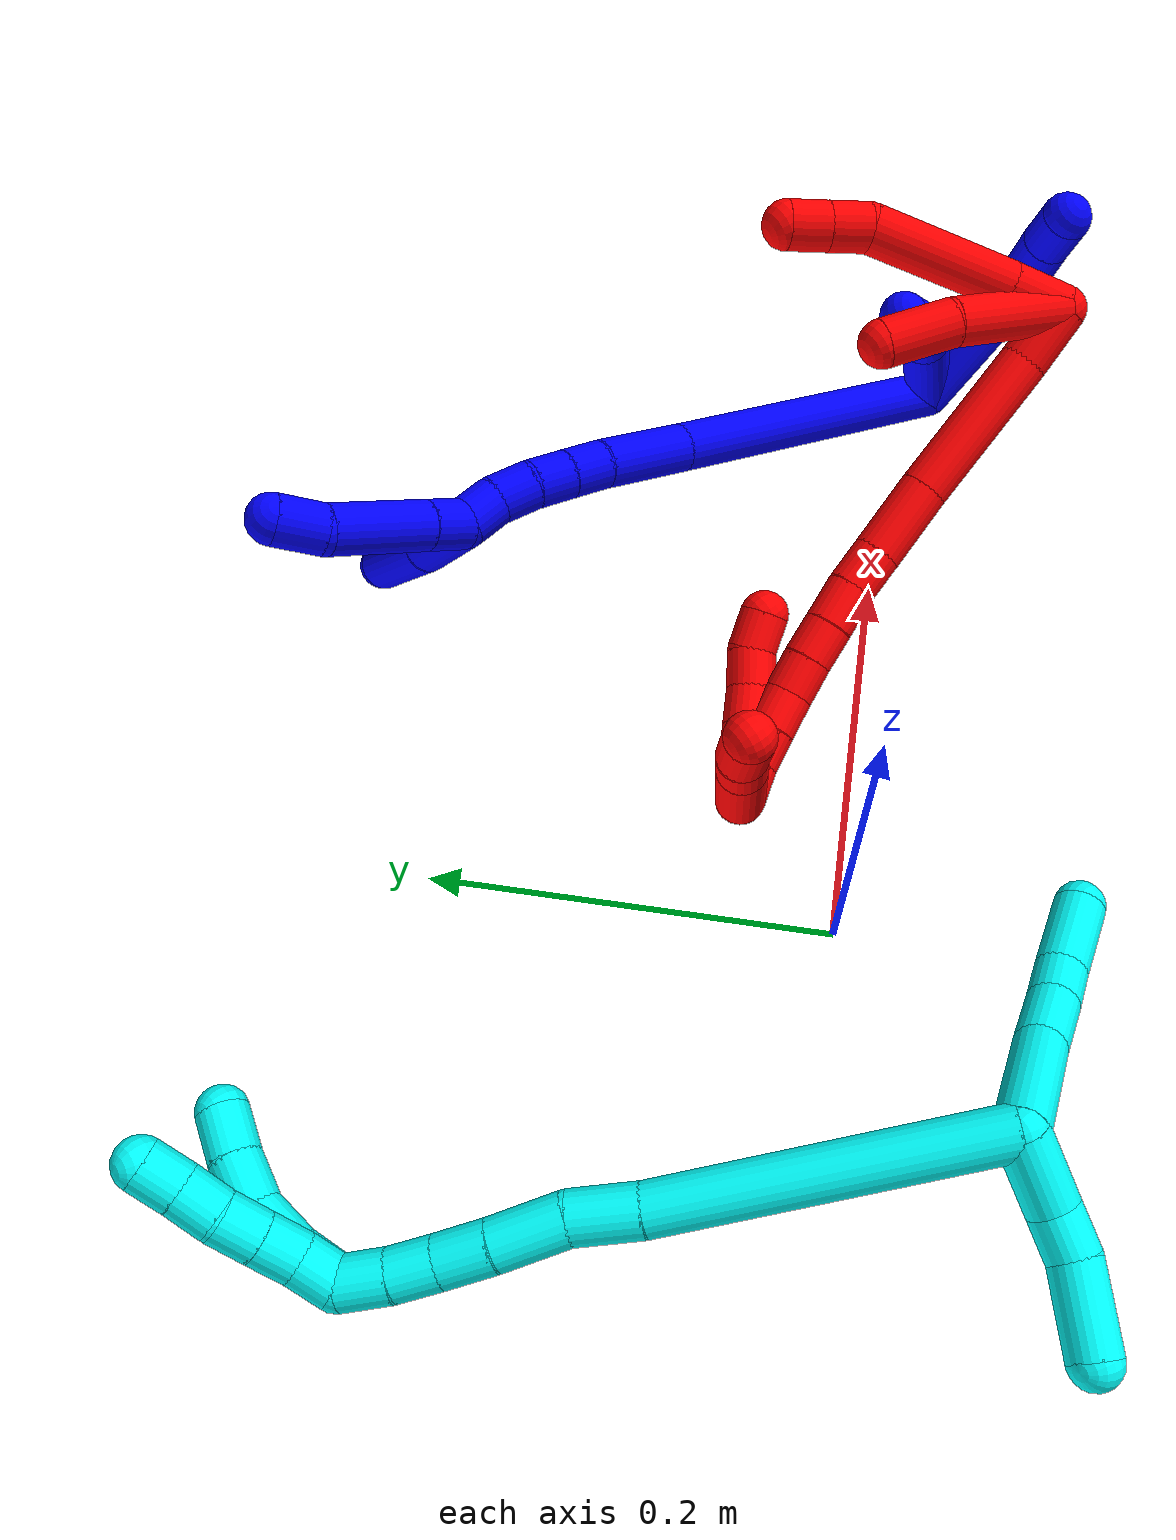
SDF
<sdf version="1.7">
 <world name="default">
  <plugin name="TubeGeneratorPlugin" filename="libtube_generator_plugin.so"/>
  <model name="photoneo_s_sensor">
   <static>1</static>
   <pose>0 0 2 1.57079 1.57079 3.14159</pose>
   <link name="link">
    <inertial><mass>0.1</mass></inertial>
    <sensor name="sensor" type="depth">
     <update_rate>30</update_rate>
     <camera>
      <horizontal_fov>1.22</horizontal_fov>
      <image><width>1920</width><height>1200</height><format>B8G8R8</format></image>
      <clip><near>0.1</near><far>4</far></clip>
      <depth_camera><output>points</output></depth_camera>
     </camera>
     <plugin name="camera_plugin" filename="libgazebo_ros_depth_camera.so">
      <baseline>0.2</baseline>
      <alwaysOn>1</alwaysOn>
      <updateRate>0.0</updateRate>
      <cameraName>camera_ir</cameraName>
      <imageTopicName>/camera/color/image_raw</imageTopicName>
      <cameraInfoTopicName>/camera/color/camera_info</cameraInfoTopicName>
      <depthImageTopicName>/camera/depth/image_raw</depthImageTopicName>
      <depthImageCameraInfoTopicName>/camera/depth/camera_info</depthImageCameraInfoTopicName>
      <pointCloudTopicName>/camera/depth/points</pointCloudTopicName>
      <frameName>fr_optical</frameName>
      <pointCloudCutoff>0.1</pointCloudCutoff>
      <pointCloudCutoffMax>2.0</pointCloudCutoffMax>
      <distortionK1>0</distortionK1>
      <distortionK2>0</distortionK2>
      <distortionK3>0</distortionK3>
      <distortionT1>0</distortionT1>
      <distortionT2>0</distortionT2>
      <CxPrime>0</CxPrime>
      <Cx>0</Cx>
      <Cy>0</Cy>
      <focalLength>0</focalLength>
      <hackBaseline>0</hackBaseline>
     </plugin>
    </sensor>
   </link>
  </model>
  <gravity>0 0 -9.8</gravity>
  <magnetic_field>6e-06 2.3e-05 -4.2e-05</magnetic_field>
  <atmosphere type="adiabatic"/>
  <physics name="default_physics" default="0" type="ode">
   <max_step_size>0.003</max_step_size>
   <real_time_factor>1</real_time_factor>
   <real_time_update_rate>1000</real_time_update_rate>
   <max_contacts>10000</max_contacts>
   <ode>
    <solver>
     <type>quick</type>
     <iters>100</iters>
     <sor>1.3</sor>
     <use_dynamic_moi_rescaling>0</use_dynamic_moi_rescaling>
    </solver>
    <constraints>
     <contact_max_correcting_vel>0</contact_max_correcting_vel>
     <contact_surface_layer>0.001</contact_surface_layer>
     <cfm>0</cfm>
     <erp>0.2</erp>
    </constraints>
   </ode>
  </physics>
  <scene><ambient>0.4 0.4 0.4 1</ambient><background>0.7 0.7 0.7 1</background><shadows>0</shadows></scene>
  <audio><device>default</device></audio>
  <spherical_coordinates>
   <surface_model>EARTH_WGS84</surface_model>
   <latitude_deg>0</latitude_deg>
   <longitude_deg>0</longitude_deg>
   <elevation>0</elevation>
   <heading_deg>0</heading_deg>
  </spherical_coordinates>
  <model name="bin">
   <static>1</static>
   <link name="bottom">
    <collision name="collision-bottom">
     <pose>0 0 -0.01 0 -0 0</pose>
     <geometry><box><size>0.8 0.6 0.02</size></box></geometry>
     <surface>
      <friction><ode><mu>100</mu><mu2>100</mu2></ode></friction>
      <contact><collide_bitmask>65535</collide_bitmask></contact>
     </surface>
    </collision>
   </link>
   <link name="west_wall">
    <collision name="collision-west_wall">
     <pose>-0.41 0 0.1 0 -0 0</pose>
     <geometry><box><size>0.02 0.6 0.2</size></box></geometry>
     <surface>
      <friction><ode><mu>100</mu><mu2>100</mu2></ode></friction>
      <contact><collide_bitmask>65535</collide_bitmask></contact>
     </surface>
    </collision>
   </link>
   <link name="east_wall">
    <collision name="collision-east_wall">
     <pose>0.41 0 0.1 0 -0 0</pose>
     <geometry><box><size>0.02 0.6 0.2</size></box></geometry>
     <surface>
      <friction><ode><mu>100</mu><mu2>100</mu2></ode></friction>
      <contact><collide_bitmask>65535</collide_bitmask></contact>
     </surface>
    </collision>
   </link>
   <link name="south_wall">
    <collision name="collision-south_wall">
     <pose>0 -0.31 0.1 0 -0 0</pose>
     <geometry><box><size>0.8 0.02 0.2</size></box></geometry>
     <surface>
      <friction><ode><mu>100</mu><mu2>100</mu2></ode></friction>
      <contact><collide_bitmask>65535</collide_bitmask></contact>
     </surface>
    </collision>
   </link>
   <link name="north_wall">
    <collision name="collision-north_wall">
     <pose>0 0.31 0.1 0 -0 0</pose>
     <geometry><box><size>0.8 0.02 0.2</size></box></geometry>
     <surface>
      <friction><ode><mu>100</mu><mu2>100</mu2></ode></friction>
      <contact><collide_bitmask>65535</collide_bitmask></contact>
     </surface>
    </collision>
   </link>
  </model>
  <model name="1">
   <static>0</static>
   <link name="1">
    <collision name="collision-cylinder-e_1_2_8">
     <pose>-0.004051 -0.002596 -0.038727 3.07467 -0.104007 -1.99852</pose>
     <geometry><cylinder><radius>0.0125</radius><length>0.078049</length></cylinder></geometry>
     <surface>
      <friction><ode><mu>1.16</mu><mu2>1.16</mu2><slip1>0</slip1><slip2>0</slip2></ode></friction>
      <contact><ode><kp>1e+06</kp><kd>1</kd><max_vel>0</max_vel><min_depth>0.001</min_depth></ode></contact>
     </surface>
    </collision>
    <visual name="visual-cylinder-e_1_2_8">
     <pose>-0.004051 -0.002596 -0.038727 3.07467 -0.104007 -1.99852</pose>
     <geometry><cylinder><radius>0.0125</radius><length>0.078049</length></cylinder></geometry>
     <material><ambient>0 0 1 1</ambient></material>
    </visual>
    <collision name="collision-cylinder-e_2_8_9">
     <pose>-0.011338 -0.001241 -0.102809 -2.98704 -0.125415 1.36275</pose>
     <geometry><cylinder><radius>0.0125</radius><length>0.05173</length></cylinder></geometry>
     <surface>
      <friction><ode><mu>1.16</mu><mu2>1.16</mu2><slip1>0</slip1><slip2>0</slip2></ode></friction>
      <contact><ode><kp>1e+06</kp><kd>1</kd><max_vel>0</max_vel><min_depth>0.001</min_depth></ode></contact>
     </surface>
    </collision>
    <visual name="visual-cylinder-e_2_8_9">
     <pose>-0.011338 -0.001241 -0.102809 -2.98704 -0.125415 1.36275</pose>
     <geometry><cylinder><radius>0.0125</radius><length>0.05173</length></cylinder></geometry>
     <material><ambient>0 0 1 1</ambient></material>
    </visual>
    <collision name="collision-cylinder-e_3_9_6">
     <pose>-0.015411 0.004072 -0.138149 -3.00588 -0.082871 1.09554</pose>
     <geometry><cylinder><radius>0.0125</radius><length>0.020221</length></cylinder></geometry>
     <surface>
      <friction><ode><mu>1.16</mu><mu2>1.16</mu2><slip1>0</slip1><slip2>0</slip2></ode></friction>
      <contact><ode><kp>1e+06</kp><kd>1</kd><max_vel>0</max_vel><min_depth>0.001</min_depth></ode></contact>
     </surface>
    </collision>
    <visual name="visual-cylinder-e_3_9_6">
     <pose>-0.015411 0.004072 -0.138149 -3.00588 -0.082871 1.09554</pose>
     <geometry><cylinder><radius>0.0125</radius><length>0.020221</length></cylinder></geometry>
     <material><ambient>0 0 1 1</ambient></material>
    </visual>
    <collision name="collision-cylinder-e_1_2_10">
     <pose>-0.008042 0.012112 -0.021745 -2.63341 -0.312521 1.09056</pose>
     <geometry><cylinder><radius>0.0125</radius><length>0.052315</length></cylinder></geometry>
     <surface>
      <friction><ode><mu>1.16</mu><mu2>1.16</mu2><slip1>0</slip1><slip2>0</slip2></ode></friction>
      <contact><ode><kp>1e+06</kp><kd>1</kd><max_vel>0</max_vel><min_depth>0.001</min_depth></ode></contact>
     </surface>
    </collision>
    <visual name="visual-cylinder-e_1_2_10">
     <pose>-0.008042 0.012112 -0.021745 -2.63341 -0.312521 1.09056</pose>
     <geometry><cylinder><radius>0.0125</radius><length>0.052315</length></cylinder></geometry>
     <material><ambient>0 0 1 1</ambient></material>
    </visual>
    <collision name="collision-cylinder-e_2_10_11">
     <pose>-0.019137 0.031538 -0.052105 -2.43761 -0.263825 0.693323</pose>
     <geometry><cylinder><radius>0.0125</radius><length>0.023411</length></cylinder></geometry>
     <surface>
      <friction><ode><mu>1.16</mu><mu2>1.16</mu2><slip1>0</slip1><slip2>0</slip2></ode></friction>
      <contact><ode><kp>1e+06</kp><kd>1</kd><max_vel>0</max_vel><min_depth>0.001</min_depth></ode></contact>
     </surface>
    </collision>
    <visual name="visual-cylinder-e_2_10_11">
     <pose>-0.019137 0.031538 -0.052105 -2.43761 -0.263825 0.693323</pose>
     <geometry><cylinder><radius>0.0125</radius><length>0.023411</length></cylinder></geometry>
     <material><ambient>0 0 1 1</ambient></material>
    </visual>
    <collision name="collision-cylinder-e_3_11_5">
     <pose>-0.024249 0.04868 -0.067535 -2.17722 -0.170471 0.32364</pose>
     <geometry><cylinder><radius>0.0125</radius><length>0.024273</length></cylinder></geometry>
     <surface>
      <friction><ode><mu>1.16</mu><mu2>1.16</mu2><slip1>0</slip1><slip2>0</slip2></ode></friction>
      <contact><ode><kp>1e+06</kp><kd>1</kd><max_vel>0</max_vel><min_depth>0.001</min_depth></ode></contact>
     </surface>
    </collision>
    <visual name="visual-cylinder-e_3_11_5">
     <pose>-0.024249 0.04868 -0.067535 -2.17722 -0.170471 0.32364</pose>
     <geometry><cylinder><radius>0.0125</radius><length>0.024273</length></cylinder></geometry>
     <material><ambient>0 0 1 1</ambient></material>
    </visual>
    <collision name="collision-cylinder-e_1_2_12">
     <pose>-0.0174 0.082013 0.00246 -1.54081 -0.208974 0.202842</pose>
     <geometry><cylinder><radius>0.0125</radius><length>0.16775</length></cylinder></geometry>
     <surface>
      <friction><ode><mu>1.16</mu><mu2>1.16</mu2><slip1>0</slip1><slip2>0</slip2></ode></friction>
      <contact><ode><kp>1e+06</kp><kd>1</kd><max_vel>0</max_vel><min_depth>0.001</min_depth></ode></contact>
     </surface>
    </collision>
    <visual name="visual-cylinder-e_1_2_12">
     <pose>-0.0174 0.082013 0.00246 -1.54081 -0.208974 0.202842</pose>
     <geometry><cylinder><radius>0.0125</radius><length>0.16775</length></cylinder></geometry>
     <material><ambient>0 0 1 1</ambient></material>
    </visual>
    <collision name="collision-cylinder-e_2_12_13">
     <pose>-0.039336 0.188706 0.003503 -1.62817 -0.181463 0.192121</pose>
     <geometry><cylinder><radius>0.0125</radius><length>0.050264</length></cylinder></geometry>
     <surface>
      <friction><ode><mu>1.16</mu><mu2>1.16</mu2><slip1>0</slip1><slip2>0</slip2></ode></friction>
      <contact><ode><kp>1e+06</kp><kd>1</kd><max_vel>0</max_vel><min_depth>0.001</min_depth></ode></contact>
     </surface>
    </collision>
    <visual name="visual-cylinder-e_2_12_13">
     <pose>-0.039336 0.188706 0.003503 -1.62817 -0.181463 0.192121</pose>
     <geometry><cylinder><radius>0.0125</radius><length>0.050264</length></cylinder></geometry>
     <material><ambient>0 0 1 1</ambient></material>
    </visual>
    <collision name="collision-cylinder-e_3_13_14">
     <pose>-0.045482 0.223605 0.002557 -1.52467 -0.156129 0.149115</pose>
     <geometry><cylinder><radius>0.0125</radius><length>0.020715</length></cylinder></geometry>
     <surface>
      <friction><ode><mu>1.16</mu><mu2>1.16</mu2><slip1>0</slip1><slip2>0</slip2></ode></friction>
      <contact><ode><kp>1e+06</kp><kd>1</kd><max_vel>0</max_vel><min_depth>0.001</min_depth></ode></contact>
     </surface>
    </collision>
    <visual name="visual-cylinder-e_3_13_14">
     <pose>-0.045482 0.223605 0.002557 -1.52467 -0.156129 0.149115</pose>
     <geometry><cylinder><radius>0.0125</radius><length>0.020715</length></cylinder></geometry>
     <material><ambient>0 0 1 1</ambient></material>
    </visual>
    <collision name="collision-cylinder-e_4_14_15">
     <pose>-0.048706 0.243664 0.003892 -1.48322 -0.161872 0.148335</pose>
     <geometry><cylinder><radius>0.0125</radius><length>0.020014</length></cylinder></geometry>
     <surface>
      <friction><ode><mu>1.16</mu><mu2>1.16</mu2><slip1>0</slip1><slip2>0</slip2></ode></friction>
      <contact><ode><kp>1e+06</kp><kd>1</kd><max_vel>0</max_vel><min_depth>0.001</min_depth></ode></contact>
     </surface>
    </collision>
    <visual name="visual-cylinder-e_4_14_15">
     <pose>-0.048706 0.243664 0.003892 -1.48322 -0.161872 0.148335</pose>
     <geometry><cylinder><radius>0.0125</radius><length>0.020014</length></cylinder></geometry>
     <material><ambient>0 0 1 1</ambient></material>
    </visual>
    <collision name="collision-cylinder-e_5_15_16">
     <pose>-0.051241 0.263684 0.007084 -1.34604 -0.088122 0.070266</pose>
     <geometry><cylinder><radius>0.0125</radius><length>0.020968</length></cylinder></geometry>
     <surface>
      <friction><ode><mu>1.16</mu><mu2>1.16</mu2><slip1>0</slip1><slip2>0</slip2></ode></friction>
      <contact><ode><kp>1e+06</kp><kd>1</kd><max_vel>0</max_vel><min_depth>0.001</min_depth></ode></contact>
     </surface>
    </collision>
    <visual name="visual-cylinder-e_5_15_16">
     <pose>-0.051241 0.263684 0.007084 -1.34604 -0.088122 0.070266</pose>
     <geometry><cylinder><radius>0.0125</radius><length>0.020968</length></cylinder></geometry>
     <material><ambient>0 0 1 1</ambient></material>
    </visual>
    <collision name="collision-cylinder-e_6_16_1">
     <pose>-0.050531 0.283787 0.01074 -1.43766 0.161687 -0.141548</pose>
     <geometry><cylinder><radius>0.0125</radius><length>0.020288</length></cylinder></geometry>
     <surface>
      <friction><ode><mu>1.16</mu><mu2>1.16</mu2><slip1>0</slip1><slip2>0</slip2></ode></friction>
      <contact><ode><kp>1e+06</kp><kd>1</kd><max_vel>0</max_vel><min_depth>0.001</min_depth></ode></contact>
     </surface>
    </collision>
    <visual name="visual-cylinder-e_6_16_1">
     <pose>-0.050531 0.283787 0.01074 -1.43766 0.161687 -0.141548</pose>
     <geometry><cylinder><radius>0.0125</radius><length>0.020288</length></cylinder></geometry>
     <material><ambient>0 0 1 1</ambient></material>
    </visual>
    <collision name="collision-cylinder-e_1_1_17">
     <pose>-0.053179 0.294023 0.033548 -0.014563 -0.196734 0.001437</pose>
     <geometry><cylinder><radius>0.0125</radius><length>0.043807</length></cylinder></geometry>
     <surface>
      <friction><ode><mu>1.16</mu><mu2>1.16</mu2><slip1>0</slip1><slip2>0</slip2></ode></friction>
      <contact><ode><kp>1e+06</kp><kd>1</kd><max_vel>0</max_vel><min_depth>0.001</min_depth></ode></contact>
     </surface>
    </collision>
    <visual name="visual-cylinder-e_1_1_17">
     <pose>-0.053179 0.294023 0.033548 -0.014563 -0.196734 0.001437</pose>
     <geometry><cylinder><radius>0.0125</radius><length>0.043807</length></cylinder></geometry>
     <material><ambient>0 0 1 1</ambient></material>
    </visual>
    <collision name="collision-cylinder-e_2_17_4">
     <pose>-0.065308 0.293729 0.081998 0.022515 -0.283042 -0.003208</pose>
     <geometry><cylinder><radius>0.0125</radius><length>0.056193</length></cylinder></geometry>
     <surface>
      <friction><ode><mu>1.16</mu><mu2>1.16</mu2><slip1>0</slip1><slip2>0</slip2></ode></friction>
      <contact><ode><kp>1e+06</kp><kd>1</kd><max_vel>0</max_vel><min_depth>0.001</min_depth></ode></contact>
     </surface>
    </collision>
    <visual name="visual-cylinder-e_2_17_4">
     <pose>-0.065308 0.293729 0.081998 0.022515 -0.283042 -0.003208</pose>
     <geometry><cylinder><radius>0.0125</radius><length>0.056193</length></cylinder></geometry>
     <material><ambient>0 0 1 1</ambient></material>
    </visual>
    <collision name="collision-cylinder-e_1_1_18">
     <pose>-0.052022 0.303964 0.010064 -1.76395 -0.290579 0.351751</pose>
     <geometry><cylinder><radius>0.0125</radius><length>0.021809</length></cylinder></geometry>
     <surface>
      <friction><ode><mu>1.16</mu><mu2>1.16</mu2><slip1>0</slip1><slip2>0</slip2></ode></friction>
      <contact><ode><kp>1e+06</kp><kd>1</kd><max_vel>0</max_vel><min_depth>0.001</min_depth></ode></contact>
     </surface>
    </collision>
    <visual name="visual-cylinder-e_1_1_18">
     <pose>-0.052022 0.303964 0.010064 -1.76395 -0.290579 0.351751</pose>
     <geometry><cylinder><radius>0.0125</radius><length>0.021809</length></cylinder></geometry>
     <material><ambient>0 0 1 1</ambient></material>
    </visual>
    <collision name="collision-cylinder-e_2_18_19">
     <pose>-0.062973 0.339479 0.003937 -1.7325 -0.296752 0.34811</pose>
     <geometry><cylinder><radius>0.0125</radius><length>0.053532</length></cylinder></geometry>
     <surface>
      <friction><ode><mu>1.16</mu><mu2>1.16</mu2><slip1>0</slip1><slip2>0</slip2></ode></friction>
      <contact><ode><kp>1e+06</kp><kd>1</kd><max_vel>0</max_vel><min_depth>0.001</min_depth></ode></contact>
     </surface>
    </collision>
    <visual name="visual-cylinder-e_2_18_19">
     <pose>-0.062973 0.339479 0.003937 -1.7325 -0.296752 0.34811</pose>
     <geometry><cylinder><radius>0.0125</radius><length>0.053532</length></cylinder></geometry>
     <material><ambient>0 0 1 1</ambient></material>
    </visual>
    <collision name="collision-cylinder-e_3_19_3">
     <pose>-0.077925 0.374786 -0.000789 -1.63099 -0.616086 0.651753</pose>
     <geometry><cylinder><radius>0.0125</radius><length>0.024658</length></cylinder></geometry>
     <surface>
      <friction><ode><mu>1.16</mu><mu2>1.16</mu2><slip1>0</slip1><slip2>0</slip2></ode></friction>
      <contact><ode><kp>1e+06</kp><kd>1</kd><max_vel>0</max_vel><min_depth>0.001</min_depth></ode></contact>
     </surface>
    </collision>
    <visual name="visual-cylinder-e_3_19_3">
     <pose>-0.077925 0.374786 -0.000789 -1.63099 -0.616086 0.651753</pose>
     <geometry><cylinder><radius>0.0125</radius><length>0.024658</length></cylinder></geometry>
     <material><ambient>0 0 1 1</ambient></material>
    </visual>
    <collision name="collision-sphere-3">
     <pose>-0.085049 0.38483 -0.001394 0 -0 0</pose>
     <geometry><sphere><radius>0.0125</radius></sphere></geometry>
     <surface>
      <friction><ode><mu>1.16</mu><mu2>1.16</mu2><slip1>0</slip1><slip2>0</slip2></ode></friction>
      <contact><ode><kp>1e+06</kp><kd>1</kd><max_vel>0</max_vel><min_depth>0.001</min_depth></ode></contact>
     </surface>
    </collision>
    <visual name="visual-sphere-3">
     <pose>-0.085049 0.38483 -0.001394 0 -0 0</pose>
     <geometry><sphere><radius>0.0125</radius></sphere></geometry>
     <material><ambient>0 0 1 1</ambient></material>
    </visual>
    <collision name="collision-sphere-19">
     <pose>-0.0708 0.364741 -0.000184 0 -0 0</pose>
     <geometry><sphere><radius>0.0125</radius></sphere></geometry>
     <surface>
      <friction><ode><mu>1.16</mu><mu2>1.16</mu2><slip1>0</slip1><slip2>0</slip2></ode></friction>
      <contact><ode><kp>1e+06</kp><kd>1</kd><max_vel>0</max_vel><min_depth>0.001</min_depth></ode></contact>
     </surface>
    </collision>
    <visual name="visual-sphere-19">
     <pose>-0.0708 0.364741 -0.000184 0 -0 0</pose>
     <geometry><sphere><radius>0.0125</radius></sphere></geometry>
     <material><ambient>0 0 1 1</ambient></material>
    </visual>
    <collision name="collision-sphere-11">
     <pose>-0.02219 0.038852 -0.060719 0 -0 0</pose>
     <geometry><sphere><radius>0.0125</radius></sphere></geometry>
     <surface>
      <friction><ode><mu>1.16</mu><mu2>1.16</mu2><slip1>0</slip1><slip2>0</slip2></ode></friction>
      <contact><ode><kp>1e+06</kp><kd>1</kd><max_vel>0</max_vel><min_depth>0.001</min_depth></ode></contact>
     </surface>
    </collision>
    <visual name="visual-sphere-11">
     <pose>-0.02219 0.038852 -0.060719 0 -0 0</pose>
     <geometry><sphere><radius>0.0125</radius></sphere></geometry>
     <material><ambient>0 0 1 1</ambient></material>
    </visual>
    <collision name="collision-sphere-10">
     <pose>-0.016085 0.024223 -0.04349 0 -0 0</pose>
     <geometry><sphere><radius>0.0125</radius></sphere></geometry>
     <surface>
      <friction><ode><mu>1.16</mu><mu2>1.16</mu2><slip1>0</slip1><slip2>0</slip2></ode></friction>
      <contact><ode><kp>1e+06</kp><kd>1</kd><max_vel>0</max_vel><min_depth>0.001</min_depth></ode></contact>
     </surface>
    </collision>
    <visual name="visual-sphere-10">
     <pose>-0.016085 0.024223 -0.04349 0 -0 0</pose>
     <geometry><sphere><radius>0.0125</radius></sphere></geometry>
     <material><ambient>0 0 1 1</ambient></material>
    </visual>
    <collision name="collision-sphere-6">
     <pose>-0.016248 0.005436 -0.148132 0 -0 0</pose>
     <geometry><sphere><radius>0.0125</radius></sphere></geometry>
     <surface>
      <friction><ode><mu>1.16</mu><mu2>1.16</mu2><slip1>0</slip1><slip2>0</slip2></ode></friction>
      <contact><ode><kp>1e+06</kp><kd>1</kd><max_vel>0</max_vel><min_depth>0.001</min_depth></ode></contact>
     </surface>
    </collision>
    <visual name="visual-sphere-6">
     <pose>-0.016248 0.005436 -0.148132 0 -0 0</pose>
     <geometry><sphere><radius>0.0125</radius></sphere></geometry>
     <material><ambient>0 0 1 1</ambient></material>
    </visual>
    <collision name="collision-sphere-9">
     <pose>-0.014574 0.002709 -0.128165 0 -0 0</pose>
     <geometry><sphere><radius>0.0125</radius></sphere></geometry>
     <surface>
      <friction><ode><mu>1.16</mu><mu2>1.16</mu2><slip1>0</slip1><slip2>0</slip2></ode></friction>
      <contact><ode><kp>1e+06</kp><kd>1</kd><max_vel>0</max_vel><min_depth>0.001</min_depth></ode></contact>
     </surface>
    </collision>
    <visual name="visual-sphere-9">
     <pose>-0.014574 0.002709 -0.128165 0 -0 0</pose>
     <geometry><sphere><radius>0.0125</radius></sphere></geometry>
     <material><ambient>0 0 1 1</ambient></material>
    </visual>
    <collision name="collision-sphere-2">
     <geometry><sphere><radius>0.0125</radius></sphere></geometry>
     <surface>
      <friction><ode><mu>1.16</mu><mu2>1.16</mu2><slip1>0</slip1><slip2>0</slip2></ode></friction>
      <contact><ode><kp>1e+06</kp><kd>1</kd><max_vel>0</max_vel><min_depth>0.001</min_depth></ode></contact>
     </surface>
    </collision>
    <visual name="visual-sphere-2">
     <geometry><sphere><radius>0.0125</radius></sphere></geometry>
     <material><ambient>0 0 1 1</ambient></material>
    </visual>
    <collision name="collision-sphere-8">
     <pose>-0.008103 -0.005191 -0.077453 0 -0 0</pose>
     <geometry><sphere><radius>0.0125</radius></sphere></geometry>
     <surface>
      <friction><ode><mu>1.16</mu><mu2>1.16</mu2><slip1>0</slip1><slip2>0</slip2></ode></friction>
      <contact><ode><kp>1e+06</kp><kd>1</kd><max_vel>0</max_vel><min_depth>0.001</min_depth></ode></contact>
     </surface>
    </collision>
    <visual name="visual-sphere-8">
     <pose>-0.008103 -0.005191 -0.077453 0 -0 0</pose>
     <geometry><sphere><radius>0.0125</radius></sphere></geometry>
     <material><ambient>0 0 1 1</ambient></material>
    </visual>
    <collision name="collision-sphere-5">
     <pose>-0.026308 0.058508 -0.074352 0 -0 0</pose>
     <geometry><sphere><radius>0.0125</radius></sphere></geometry>
     <surface>
      <friction><ode><mu>1.16</mu><mu2>1.16</mu2><slip1>0</slip1><slip2>0</slip2></ode></friction>
      <contact><ode><kp>1e+06</kp><kd>1</kd><max_vel>0</max_vel><min_depth>0.001</min_depth></ode></contact>
     </surface>
    </collision>
    <visual name="visual-sphere-5">
     <pose>-0.026308 0.058508 -0.074352 0 -0 0</pose>
     <geometry><sphere><radius>0.0125</radius></sphere></geometry>
     <material><ambient>0 0 1 1</ambient></material>
    </visual>
    <collision name="collision-sphere-12">
     <pose>-0.034801 0.164027 0.00492 0 -0 0</pose>
     <geometry><sphere><radius>0.0125</radius></sphere></geometry>
     <surface>
      <friction><ode><mu>1.16</mu><mu2>1.16</mu2><slip1>0</slip1><slip2>0</slip2></ode></friction>
      <contact><ode><kp>1e+06</kp><kd>1</kd><max_vel>0</max_vel><min_depth>0.001</min_depth></ode></contact>
     </surface>
    </collision>
    <visual name="visual-sphere-12">
     <pose>-0.034801 0.164027 0.00492 0 -0 0</pose>
     <geometry><sphere><radius>0.0125</radius></sphere></geometry>
     <material><ambient>0 0 1 1</ambient></material>
    </visual>
    <collision name="collision-sphere-13">
     <pose>-0.043872 0.213385 0.002085 0 -0 0</pose>
     <geometry><sphere><radius>0.0125</radius></sphere></geometry>
     <surface>
      <friction><ode><mu>1.16</mu><mu2>1.16</mu2><slip1>0</slip1><slip2>0</slip2></ode></friction>
      <contact><ode><kp>1e+06</kp><kd>1</kd><max_vel>0</max_vel><min_depth>0.001</min_depth></ode></contact>
     </surface>
    </collision>
    <visual name="visual-sphere-13">
     <pose>-0.043872 0.213385 0.002085 0 -0 0</pose>
     <geometry><sphere><radius>0.0125</radius></sphere></geometry>
     <material><ambient>0 0 1 1</ambient></material>
    </visual>
    <collision name="collision-sphere-14">
     <pose>-0.047093 0.233826 0.003029 0 -0 0</pose>
     <geometry><sphere><radius>0.0125</radius></sphere></geometry>
     <surface>
      <friction><ode><mu>1.16</mu><mu2>1.16</mu2><slip1>0</slip1><slip2>0</slip2></ode></friction>
      <contact><ode><kp>1e+06</kp><kd>1</kd><max_vel>0</max_vel><min_depth>0.001</min_depth></ode></contact>
     </surface>
    </collision>
    <visual name="visual-sphere-14">
     <pose>-0.047093 0.233826 0.003029 0 -0 0</pose>
     <geometry><sphere><radius>0.0125</radius></sphere></geometry>
     <material><ambient>0 0 1 1</ambient></material>
    </visual>
    <collision name="collision-sphere-15">
     <pose>-0.050319 0.253503 0.004756 0 -0 0</pose>
     <geometry><sphere><radius>0.0125</radius></sphere></geometry>
     <surface>
      <friction><ode><mu>1.16</mu><mu2>1.16</mu2><slip1>0</slip1><slip2>0</slip2></ode></friction>
      <contact><ode><kp>1e+06</kp><kd>1</kd><max_vel>0</max_vel><min_depth>0.001</min_depth></ode></contact>
     </surface>
    </collision>
    <visual name="visual-sphere-15">
     <pose>-0.050319 0.253503 0.004756 0 -0 0</pose>
     <geometry><sphere><radius>0.0125</radius></sphere></geometry>
     <material><ambient>0 0 1 1</ambient></material>
    </visual>
    <collision name="collision-sphere-16">
     <pose>-0.052164 0.273864 0.009411 0 -0 0</pose>
     <geometry><sphere><radius>0.0125</radius></sphere></geometry>
     <surface>
      <friction><ode><mu>1.16</mu><mu2>1.16</mu2><slip1>0</slip1><slip2>0</slip2></ode></friction>
      <contact><ode><kp>1e+06</kp><kd>1</kd><max_vel>0</max_vel><min_depth>0.001</min_depth></ode></contact>
     </surface>
    </collision>
    <visual name="visual-sphere-16">
     <pose>-0.052164 0.273864 0.009411 0 -0 0</pose>
     <geometry><sphere><radius>0.0125</radius></sphere></geometry>
     <material><ambient>0 0 1 1</ambient></material>
    </visual>
    <collision name="collision-sphere-1">
     <pose>-0.048898 0.29371 0.012069 0 -0 0</pose>
     <geometry><sphere><radius>0.0125</radius></sphere></geometry>
     <surface>
      <friction><ode><mu>1.16</mu><mu2>1.16</mu2><slip1>0</slip1><slip2>0</slip2></ode></friction>
      <contact><ode><kp>1e+06</kp><kd>1</kd><max_vel>0</max_vel><min_depth>0.001</min_depth></ode></contact>
     </surface>
    </collision>
    <visual name="visual-sphere-1">
     <pose>-0.048898 0.29371 0.012069 0 -0 0</pose>
     <geometry><sphere><radius>0.0125</radius></sphere></geometry>
     <material><ambient>0 0 1 1</ambient></material>
    </visual>
    <collision name="collision-sphere-18">
     <pose>-0.055147 0.314217 0.008058 0 -0 0</pose>
     <geometry><sphere><radius>0.0125</radius></sphere></geometry>
     <surface>
      <friction><ode><mu>1.16</mu><mu2>1.16</mu2><slip1>0</slip1><slip2>0</slip2></ode></friction>
      <contact><ode><kp>1e+06</kp><kd>1</kd><max_vel>0</max_vel><min_depth>0.001</min_depth></ode></contact>
     </surface>
    </collision>
    <visual name="visual-sphere-18">
     <pose>-0.055147 0.314217 0.008058 0 -0 0</pose>
     <geometry><sphere><radius>0.0125</radius></sphere></geometry>
     <material><ambient>0 0 1 1</ambient></material>
    </visual>
    <collision name="collision-sphere-17">
     <pose>-0.057461 0.294336 0.055027 0 -0 0</pose>
     <geometry><sphere><radius>0.0125</radius></sphere></geometry>
     <surface>
      <friction><ode><mu>1.16</mu><mu2>1.16</mu2><slip1>0</slip1><slip2>0</slip2></ode></friction>
      <contact><ode><kp>1e+06</kp><kd>1</kd><max_vel>0</max_vel><min_depth>0.001</min_depth></ode></contact>
     </surface>
    </collision>
    <visual name="visual-sphere-17">
     <pose>-0.057461 0.294336 0.055027 0 -0 0</pose>
     <geometry><sphere><radius>0.0125</radius></sphere></geometry>
     <material><ambient>0 0 1 1</ambient></material>
    </visual>
    <collision name="collision-sphere-4">
     <pose>-0.073154 0.293121 0.10897 0 -0 0</pose>
     <geometry><sphere><radius>0.0125</radius></sphere></geometry>
     <surface>
      <friction><ode><mu>1.16</mu><mu2>1.16</mu2><slip1>0</slip1><slip2>0</slip2></ode></friction>
      <contact><ode><kp>1e+06</kp><kd>1</kd><max_vel>0</max_vel><min_depth>0.001</min_depth></ode></contact>
     </surface>
    </collision>
    <visual name="visual-sphere-4">
     <pose>-0.073154 0.293121 0.10897 0 -0 0</pose>
     <geometry><sphere><radius>0.0125</radius></sphere></geometry>
     <material><ambient>0 0 1 1</ambient></material>
    </visual>
    <inertial>
     <pose>-0.032015 0.146449 -0.010076 0 -0 0</pose>
     <mass>0.75</mass>
     <inertia>
      <ixx>0.000504</ixx>
      <ixy>0</ixy>
      <ixz>0</ixz>
      <iyy>0.000176</iyy>
      <iyz>0</iyz>
      <izz>-0.000336</izz>
     </inertia>
    </inertial>
   </link>
   <pose>0.328062 -0.021076 0.01149 2.86578 0.329726 -2.38228</pose>
  </model>
  <model name="2">
   <static>0</static>
   <link name="2">
    <collision name="collision-cylinder-e_1_2_8">
     <pose>0.01208 0.001166 -0.009329 -3.0172 0.909456 -2.8882</pose>
     <geometry><cylinder><radius>0.0125</radius><length>0.030615</length></cylinder></geometry>
     <surface>
      <friction><ode><mu>1.16</mu><mu2>1.16</mu2><slip1>0</slip1><slip2>0</slip2></ode></friction>
      <contact><ode><kp>1e+06</kp><kd>1</kd><max_vel>0</max_vel><min_depth>0.001</min_depth></ode></contact>
     </surface>
    </collision>
    <visual name="visual-cylinder-e_1_2_8">
     <pose>0.01208 0.001166 -0.009329 -3.0172 0.909456 -2.8882</pose>
     <geometry><cylinder><radius>0.0125</radius><length>0.030615</length></cylinder></geometry>
     <material><ambient>1 0 0 1</ambient></material>
    </visual>
    <collision name="collision-cylinder-e_2_8_9">
     <pose>0.053519 0.006621 -0.043792 -2.97259 0.855669 -2.77428</pose>
     <geometry><cylinder><radius>0.0125</radius><length>0.07777</length></cylinder></geometry>
     <surface>
      <friction><ode><mu>1.16</mu><mu2>1.16</mu2><slip1>0</slip1><slip2>0</slip2></ode></friction>
      <contact><ode><kp>1e+06</kp><kd>1</kd><max_vel>0</max_vel><min_depth>0.001</min_depth></ode></contact>
     </surface>
    </collision>
    <visual name="visual-cylinder-e_2_8_9">
     <pose>0.053519 0.006621 -0.043792 -2.97259 0.855669 -2.77428</pose>
     <geometry><cylinder><radius>0.0125</radius><length>0.07777</length></cylinder></geometry>
     <material><ambient>1 0 0 1</ambient></material>
    </visual>
    <collision name="collision-cylinder-e_3_9_10">
     <pose>0.088346 0.010868 -0.077873 3.13685 0.548646 3.12476</pose>
     <geometry><cylinder><radius>0.0125</radius><length>0.020971</length></cylinder></geometry>
     <surface>
      <friction><ode><mu>1.16</mu><mu2>1.16</mu2><slip1>0</slip1><slip2>0</slip2></ode></friction>
      <contact><ode><kp>1e+06</kp><kd>1</kd><max_vel>0</max_vel><min_depth>0.001</min_depth></ode></contact>
     </surface>
    </collision>
    <visual name="visual-cylinder-e_3_9_10">
     <pose>0.088346 0.010868 -0.077873 3.13685 0.548646 3.12476</pose>
     <geometry><cylinder><radius>0.0125</radius><length>0.020971</length></cylinder></geometry>
     <material><ambient>1 0 0 1</ambient></material>
    </visual>
    <collision name="collision-cylinder-e_4_10_6">
     <pose>0.099165 0.010939 -0.095645 -3.12873 0.544944 -3.09557</pose>
     <geometry><cylinder><radius>0.0125</radius><length>0.020644</length></cylinder></geometry>
     <surface>
      <friction><ode><mu>1.16</mu><mu2>1.16</mu2><slip1>0</slip1><slip2>0</slip2></ode></friction>
      <contact><ode><kp>1e+06</kp><kd>1</kd><max_vel>0</max_vel><min_depth>0.001</min_depth></ode></contact>
     </surface>
    </collision>
    <visual name="visual-cylinder-e_4_10_6">
     <pose>0.099165 0.010939 -0.095645 -3.12873 0.544944 -3.09557</pose>
     <geometry><cylinder><radius>0.0125</radius><length>0.020644</length></cylinder></geometry>
     <material><ambient>1 0 0 1</ambient></material>
    </visual>
    <collision name="collision-cylinder-e_1_2_11">
     <pose>0.010942 0.003315 -0.028623 -3.02628 0.362908 -2.532</pose>
     <geometry><cylinder><radius>0.0125</radius><length>0.061644</length></cylinder></geometry>
     <surface>
      <friction><ode><mu>1.16</mu><mu2>1.16</mu2><slip1>0</slip1><slip2>0</slip2></ode></friction>
      <contact><ode><kp>1e+06</kp><kd>1</kd><max_vel>0</max_vel><min_depth>0.001</min_depth></ode></contact>
     </surface>
    </collision>
    <visual name="visual-cylinder-e_1_2_11">
     <pose>0.010942 0.003315 -0.028623 -3.02628 0.362908 -2.532</pose>
     <geometry><cylinder><radius>0.0125</radius><length>0.061644</length></cylinder></geometry>
     <material><ambient>1 0 0 1</ambient></material>
    </visual>
    <collision name="collision-cylinder-e_2_11_5">
     <pose>0.026552 0.006112 -0.07584 3.11371 0.245896 2.91689</pose>
     <geometry><cylinder><radius>0.0125</radius><length>0.038356</length></cylinder></geometry>
     <surface>
      <friction><ode><mu>1.16</mu><mu2>1.16</mu2><slip1>0</slip1><slip2>0</slip2></ode></friction>
      <contact><ode><kp>1e+06</kp><kd>1</kd><max_vel>0</max_vel><min_depth>0.001</min_depth></ode></contact>
     </surface>
    </collision>
    <visual name="visual-cylinder-e_2_11_5">
     <pose>0.026552 0.006112 -0.07584 3.11371 0.245896 2.91689</pose>
     <geometry><cylinder><radius>0.0125</radius><length>0.038356</length></cylinder></geometry>
     <material><ambient>1 0 0 1</ambient></material>
    </visual>
    <collision name="collision-cylinder-e_1_2_12">
     <pose>-0.005672 -0.005806 -0.013886 2.74559 -0.360372 -1.47438</pose>
     <geometry><cylinder><radius>0.0125</radius><length>0.032168</length></cylinder></geometry>
     <surface>
      <friction><ode><mu>1.16</mu><mu2>1.16</mu2><slip1>0</slip1><slip2>0</slip2></ode></friction>
      <contact><ode><kp>1e+06</kp><kd>1</kd><max_vel>0</max_vel><min_depth>0.001</min_depth></ode></contact>
     </surface>
    </collision>
    <visual name="visual-cylinder-e_1_2_12">
     <pose>-0.005672 -0.005806 -0.013886 2.74559 -0.360372 -1.47438</pose>
     <geometry><cylinder><radius>0.0125</radius><length>0.032168</length></cylinder></geometry>
     <material><ambient>1 0 0 1</ambient></material>
    </visual>
    <collision name="collision-cylinder-e_2_12_13">
     <pose>-0.024459 -0.020697 -0.065415 2.90474 -0.326577 -1.89069</pose>
     <geometry><cylinder><radius>0.0125</radius><length>0.081768</length></cylinder></geometry>
     <surface>
      <friction><ode><mu>1.16</mu><mu2>1.16</mu2><slip1>0</slip1><slip2>0</slip2></ode></friction>
      <contact><ode><kp>1e+06</kp><kd>1</kd><max_vel>0</max_vel><min_depth>0.001</min_depth></ode></contact>
     </surface>
    </collision>
    <visual name="visual-cylinder-e_2_12_13">
     <pose>-0.024459 -0.020697 -0.065415 2.90474 -0.326577 -1.89069</pose>
     <geometry><cylinder><radius>0.0125</radius><length>0.081768</length></cylinder></geometry>
     <material><ambient>1 0 0 1</ambient></material>
    </visual>
    <collision name="collision-cylinder-e_3_13_14">
     <pose>-0.0447 -0.033905 -0.121564 2.92249 -0.359462 -2.05285</pose>
     <geometry><cylinder><radius>0.0125</radius><length>0.04051</length></cylinder></geometry>
     <surface>
      <friction><ode><mu>1.16</mu><mu2>1.16</mu2><slip1>0</slip1><slip2>0</slip2></ode></friction>
      <contact><ode><kp>1e+06</kp><kd>1</kd><max_vel>0</max_vel><min_depth>0.001</min_depth></ode></contact>
     </surface>
    </collision>
    <visual name="visual-cylinder-e_3_13_14">
     <pose>-0.0447 -0.033905 -0.121564 2.92249 -0.359462 -2.05285</pose>
     <geometry><cylinder><radius>0.0125</radius><length>0.04051</length></cylinder></geometry>
     <material><ambient>1 0 0 1</ambient></material>
    </visual>
    <collision name="collision-cylinder-e_4_14_15">
     <pose>-0.055635 -0.039723 -0.150333 2.97767 -0.351144 -2.27427</pose>
     <geometry><cylinder><radius>0.0125</radius><length>0.022156</length></cylinder></geometry>
     <surface>
      <friction><ode><mu>1.16</mu><mu2>1.16</mu2><slip1>0</slip1><slip2>0</slip2></ode></friction>
      <contact><ode><kp>1e+06</kp><kd>1</kd><max_vel>0</max_vel><min_depth>0.001</min_depth></ode></contact>
     </surface>
    </collision>
    <visual name="visual-cylinder-e_4_14_15">
     <pose>-0.055635 -0.039723 -0.150333 2.97767 -0.351144 -2.27427</pose>
     <geometry><cylinder><radius>0.0125</radius><length>0.022156</length></cylinder></geometry>
     <material><ambient>1 0 0 1</ambient></material>
    </visual>
    <collision name="collision-cylinder-e_5_15_16">
     <pose>-0.064298 -0.042737 -0.170741 3.01258 -0.442915 -2.58281</pose>
     <geometry><cylinder><radius>0.0125</radius><length>0.022645</length></cylinder></geometry>
     <surface>
      <friction><ode><mu>1.16</mu><mu2>1.16</mu2><slip1>0</slip1><slip2>0</slip2></ode></friction>
      <contact><ode><kp>1e+06</kp><kd>1</kd><max_vel>0</max_vel><min_depth>0.001</min_depth></ode></contact>
     </surface>
    </collision>
    <visual name="visual-cylinder-e_5_15_16">
     <pose>-0.064298 -0.042737 -0.170741 3.01258 -0.442915 -2.58281</pose>
     <geometry><cylinder><radius>0.0125</radius><length>0.022645</length></cylinder></geometry>
     <material><ambient>1 0 0 1</ambient></material>
    </visual>
    <collision name="collision-cylinder-e_6_16_17">
     <pose>-0.073435 -0.045744 -0.189865 2.95541 -0.438416 -2.34795</pose>
     <geometry><cylinder><radius>0.0125</radius><length>0.020184</length></cylinder></geometry>
     <surface>
      <friction><ode><mu>1.16</mu><mu2>1.16</mu2><slip1>0</slip1><slip2>0</slip2></ode></friction>
      <contact><ode><kp>1e+06</kp><kd>1</kd><max_vel>0</max_vel><min_depth>0.001</min_depth></ode></contact>
     </surface>
    </collision>
    <visual name="visual-cylinder-e_6_16_17">
     <pose>-0.073435 -0.045744 -0.189865 2.95541 -0.438416 -2.34795</pose>
     <geometry><cylinder><radius>0.0125</radius><length>0.020184</length></cylinder></geometry>
     <material><ambient>1 0 0 1</ambient></material>
    </visual>
    <collision name="collision-cylinder-e_7_17_18">
     <pose>-0.082426 -0.049317 -0.207507 2.92777 -0.488081 -2.32771</pose>
     <geometry><cylinder><radius>0.0125</radius><length>0.020073</length></cylinder></geometry>
     <surface>
      <friction><ode><mu>1.16</mu><mu2>1.16</mu2><slip1>0</slip1><slip2>0</slip2></ode></friction>
      <contact><ode><kp>1e+06</kp><kd>1</kd><max_vel>0</max_vel><min_depth>0.001</min_depth></ode></contact>
     </surface>
    </collision>
    <visual name="visual-cylinder-e_7_17_18">
     <pose>-0.082426 -0.049317 -0.207507 2.92777 -0.488081 -2.32771</pose>
     <geometry><cylinder><radius>0.0125</radius><length>0.020073</length></cylinder></geometry>
     <material><ambient>1 0 0 1</ambient></material>
    </visual>
    <collision name="collision-cylinder-e_8_18_19">
     <pose>-0.09198 -0.051701 -0.225067 3.08506 -0.498222 -2.92023</pose>
     <geometry><cylinder><radius>0.0125</radius><length>0.020288</length></cylinder></geometry>
     <surface>
      <friction><ode><mu>1.16</mu><mu2>1.16</mu2><slip1>0</slip1><slip2>0</slip2></ode></friction>
      <contact><ode><kp>1e+06</kp><kd>1</kd><max_vel>0</max_vel><min_depth>0.001</min_depth></ode></contact>
     </surface>
    </collision>
    <visual name="visual-cylinder-e_8_18_19">
     <pose>-0.09198 -0.051701 -0.225067 3.08506 -0.498222 -2.92023</pose>
     <geometry><cylinder><radius>0.0125</radius><length>0.020288</length></cylinder></geometry>
     <material><ambient>1 0 0 1</ambient></material>
    </visual>
    <collision name="collision-cylinder-e_9_19_20">
     <pose>-0.101848 -0.053175 -0.242586 3.02958 -0.524624 -2.72989</pose>
     <geometry><cylinder><radius>0.0125</radius><length>0.02005</length></cylinder></geometry>
     <surface>
      <friction><ode><mu>1.16</mu><mu2>1.16</mu2><slip1>0</slip1><slip2>0</slip2></ode></friction>
      <contact><ode><kp>1e+06</kp><kd>1</kd><max_vel>0</max_vel><min_depth>0.001</min_depth></ode></contact>
     </surface>
    </collision>
    <visual name="visual-cylinder-e_9_19_20">
     <pose>-0.101848 -0.053175 -0.242586 3.02958 -0.524624 -2.72989</pose>
     <geometry><cylinder><radius>0.0125</radius><length>0.02005</length></cylinder></geometry>
     <material><ambient>1 0 0 1</ambient></material>
    </visual>
    <collision name="collision-cylinder-e_10_20_1">
     <pose>-0.112334 -0.051815 -0.259351 -2.8629 -0.572965 2.25289</pose>
     <geometry><cylinder><radius>0.0125</radius><length>0.020158</length></cylinder></geometry>
     <surface>
      <friction><ode><mu>1.16</mu><mu2>1.16</mu2><slip1>0</slip1><slip2>0</slip2></ode></friction>
      <contact><ode><kp>1e+06</kp><kd>1</kd><max_vel>0</max_vel><min_depth>0.001</min_depth></ode></contact>
     </surface>
    </collision>
    <visual name="visual-cylinder-e_10_20_1">
     <pose>-0.112334 -0.051815 -0.259351 -2.8629 -0.572965 2.25289</pose>
     <geometry><cylinder><radius>0.0125</radius><length>0.020158</length></cylinder></geometry>
     <material><ambient>1 0 0 1</ambient></material>
    </visual>
    <collision name="collision-cylinder-e_1_1_21">
     <pose>-0.111571 -0.024079 -0.269473 -1.64855 0.23967 -0.258861</pose>
     <geometry><cylinder><radius>0.0125</radius><length>0.052465</length></cylinder></geometry>
     <surface>
      <friction><ode><mu>1.16</mu><mu2>1.16</mu2><slip1>0</slip1><slip2>0</slip2></ode></friction>
      <contact><ode><kp>1e+06</kp><kd>1</kd><max_vel>0</max_vel><min_depth>0.001</min_depth></ode></contact>
     </surface>
    </collision>
    <visual name="visual-cylinder-e_1_1_21">
     <pose>-0.111571 -0.024079 -0.269473 -1.64855 0.23967 -0.258861</pose>
     <geometry><cylinder><radius>0.0125</radius><length>0.052465</length></cylinder></geometry>
     <material><ambient>1 0 0 1</ambient></material>
    </visual>
    <collision name="collision-cylinder-e_2_21_22">
     <pose>-0.102844 0.011075 -0.272299 -1.65741 0.250106 -0.272495</pose>
     <geometry><cylinder><radius>0.0125</radius><length>0.020199</length></cylinder></geometry>
     <surface>
      <friction><ode><mu>1.16</mu><mu2>1.16</mu2><slip1>0</slip1><slip2>0</slip2></ode></friction>
      <contact><ode><kp>1e+06</kp><kd>1</kd><max_vel>0</max_vel><min_depth>0.001</min_depth></ode></contact>
     </surface>
    </collision>
    <visual name="visual-cylinder-e_2_21_22">
     <pose>-0.102844 0.011075 -0.272299 -1.65741 0.250106 -0.272495</pose>
     <geometry><cylinder><radius>0.0125</radius><length>0.020199</length></cylinder></geometry>
     <material><ambient>1 0 0 1</ambient></material>
    </visual>
    <collision name="collision-cylinder-e_3_22_4">
     <pose>-0.097722 0.034234 -0.272823 -1.5468 0.193044 -0.188493</pose>
     <geometry><cylinder><radius>0.0125</radius><length>0.027336</length></cylinder></geometry>
     <surface>
      <friction><ode><mu>1.16</mu><mu2>1.16</mu2><slip1>0</slip1><slip2>0</slip2></ode></friction>
      <contact><ode><kp>1e+06</kp><kd>1</kd><max_vel>0</max_vel><min_depth>0.001</min_depth></ode></contact>
     </surface>
    </collision>
    <visual name="visual-cylinder-e_3_22_4">
     <pose>-0.097722 0.034234 -0.272823 -1.5468 0.193044 -0.188493</pose>
     <geometry><cylinder><radius>0.0125</radius><length>0.027336</length></cylinder></geometry>
     <material><ambient>1 0 0 1</ambient></material>
    </visual>
    <collision name="collision-cylinder-e_1_1_23">
     <pose>-0.111048 -0.052861 -0.260933 0.475256 0.740924 0.18759</pose>
     <geometry><cylinder><radius>0.0125</radius><length>0.02</length></cylinder></geometry>
     <surface>
      <friction><ode><mu>1.16</mu><mu2>1.16</mu2><slip1>0</slip1><slip2>0</slip2></ode></friction>
      <contact><ode><kp>1e+06</kp><kd>1</kd><max_vel>0</max_vel><min_depth>0.001</min_depth></ode></contact>
     </surface>
    </collision>
    <visual name="visual-cylinder-e_1_1_23">
     <pose>-0.111048 -0.052861 -0.260933 0.475256 0.740924 0.18759</pose>
     <geometry><cylinder><radius>0.0125</radius><length>0.02</length></cylinder></geometry>
     <material><ambient>1 0 0 1</ambient></material>
    </visual>
    <collision name="collision-cylinder-e_2_23_24">
     <pose>-0.096775 -0.057481 -0.247903 0.190013 0.851639 0.086391</pose>
     <geometry><cylinder><radius>0.0125</radius><length>0.02</length></cylinder></geometry>
     <surface>
      <friction><ode><mu>1.16</mu><mu2>1.16</mu2><slip1>0</slip1><slip2>0</slip2></ode></friction>
      <contact><ode><kp>1e+06</kp><kd>1</kd><max_vel>0</max_vel><min_depth>0.001</min_depth></ode></contact>
     </surface>
    </collision>
    <visual name="visual-cylinder-e_2_23_24">
     <pose>-0.096775 -0.057481 -0.247903 0.190013 0.851639 0.086391</pose>
     <geometry><cylinder><radius>0.0125</radius><length>0.02</length></cylinder></geometry>
     <material><ambient>1 0 0 1</ambient></material>
    </visual>
    <collision name="collision-cylinder-e_3_24_25">
     <pose>-0.081863 -0.059962 -0.234809 0.184529 0.831288 0.08163</pose>
     <geometry><cylinder><radius>0.0125</radius><length>0.02</length></cylinder></geometry>
     <surface>
      <friction><ode><mu>1.16</mu><mu2>1.16</mu2><slip1>0</slip1><slip2>0</slip2></ode></friction>
      <contact><ode><kp>1e+06</kp><kd>1</kd><max_vel>0</max_vel><min_depth>0.001</min_depth></ode></contact>
     </surface>
    </collision>
    <visual name="visual-cylinder-e_3_24_25">
     <pose>-0.081863 -0.059962 -0.234809 0.184529 0.831288 0.08163</pose>
     <geometry><cylinder><radius>0.0125</radius><length>0.02</length></cylinder></geometry>
     <material><ambient>1 0 0 1</ambient></material>
    </visual>
    <collision name="collision-cylinder-e_4_25_26">
     <pose>-0.066308 -0.061281 -0.222414 0.014305 0.955669 0.007408</pose>
     <geometry><cylinder><radius>0.0125</radius><length>0.02</length></cylinder></geometry>
     <surface>
      <friction><ode><mu>1.16</mu><mu2>1.16</mu2><slip1>0</slip1><slip2>0</slip2></ode></friction>
      <contact><ode><kp>1e+06</kp><kd>1</kd><max_vel>0</max_vel><min_depth>0.001</min_depth></ode></contact>
     </surface>
    </collision>
    <visual name="visual-cylinder-e_4_25_26">
     <pose>-0.066308 -0.061281 -0.222414 0.014305 0.955669 0.007408</pose>
     <geometry><cylinder><radius>0.0125</radius><length>0.02</length></cylinder></geometry>
     <material><ambient>1 0 0 1</ambient></material>
    </visual>
    <collision name="collision-cylinder-e_5_26_3">
     <pose>-0.052049 -0.059616 -0.208909 -0.2222 0.655082 -0.075775</pose>
     <geometry><cylinder><radius>0.0125</radius><length>0.02</length></cylinder></geometry>
     <surface>
      <friction><ode><mu>1.16</mu><mu2>1.16</mu2><slip1>0</slip1><slip2>0</slip2></ode></friction>
      <contact><ode><kp>1e+06</kp><kd>1</kd><max_vel>0</max_vel><min_depth>0.001</min_depth></ode></contact>
     </surface>
    </collision>
    <visual name="visual-cylinder-e_5_26_3">
     <pose>-0.052049 -0.059616 -0.208909 -0.2222 0.655082 -0.075775</pose>
     <geometry><cylinder><radius>0.0125</radius><length>0.02</length></cylinder></geometry>
     <material><ambient>1 0 0 1</ambient></material>
    </visual>
    <collision name="collision-sphere-3">
     <pose>-0.045957 -0.057868 -0.201174 0 -0 0</pose>
     <geometry><sphere><radius>0.0125</radius></sphere></geometry>
     <surface>
      <friction><ode><mu>1.16</mu><mu2>1.16</mu2><slip1>0</slip1><slip2>0</slip2></ode></friction>
      <contact><ode><kp>1e+06</kp><kd>1</kd><max_vel>0</max_vel><min_depth>0.001</min_depth></ode></contact>
     </surface>
    </collision>
    <visual name="visual-sphere-3">
     <pose>-0.045957 -0.057868 -0.201174 0 -0 0</pose>
     <geometry><sphere><radius>0.0125</radius></sphere></geometry>
     <material><ambient>1 0 0 1</ambient></material>
    </visual>
    <collision name="collision-sphere-26">
     <pose>-0.058141 -0.061364 -0.216644 0 -0 0</pose>
     <geometry><sphere><radius>0.0125</radius></sphere></geometry>
     <surface>
      <friction><ode><mu>1.16</mu><mu2>1.16</mu2><slip1>0</slip1><slip2>0</slip2></ode></friction>
      <contact><ode><kp>1e+06</kp><kd>1</kd><max_vel>0</max_vel><min_depth>0.001</min_depth></ode></contact>
     </surface>
    </collision>
    <visual name="visual-sphere-26">
     <pose>-0.058141 -0.061364 -0.216644 0 -0 0</pose>
     <geometry><sphere><radius>0.0125</radius></sphere></geometry>
     <material><ambient>1 0 0 1</ambient></material>
    </visual>
    <collision name="collision-sphere-25">
     <pose>-0.074475 -0.061198 -0.228184 0 -0 0</pose>
     <geometry><sphere><radius>0.0125</radius></sphere></geometry>
     <surface>
      <friction><ode><mu>1.16</mu><mu2>1.16</mu2><slip1>0</slip1><slip2>0</slip2></ode></friction>
      <contact><ode><kp>1e+06</kp><kd>1</kd><max_vel>0</max_vel><min_depth>0.001</min_depth></ode></contact>
     </surface>
    </collision>
    <visual name="visual-sphere-25">
     <pose>-0.074475 -0.061198 -0.228184 0 -0 0</pose>
     <geometry><sphere><radius>0.0125</radius></sphere></geometry>
     <material><ambient>1 0 0 1</ambient></material>
    </visual>
    <collision name="collision-sphere-24">
     <pose>-0.089251 -0.058725 -0.241434 0 -0 0</pose>
     <geometry><sphere><radius>0.0125</radius></sphere></geometry>
     <surface>
      <friction><ode><mu>1.16</mu><mu2>1.16</mu2><slip1>0</slip1><slip2>0</slip2></ode></friction>
      <contact><ode><kp>1e+06</kp><kd>1</kd><max_vel>0</max_vel><min_depth>0.001</min_depth></ode></contact>
     </surface>
    </collision>
    <visual name="visual-sphere-24">
     <pose>-0.089251 -0.058725 -0.241434 0 -0 0</pose>
     <geometry><sphere><radius>0.0125</radius></sphere></geometry>
     <material><ambient>1 0 0 1</ambient></material>
    </visual>
    <collision name="collision-sphere-23">
     <pose>-0.104298 -0.056237 -0.254372 0 -0 0</pose>
     <geometry><sphere><radius>0.0125</radius></sphere></geometry>
     <surface>
      <friction><ode><mu>1.16</mu><mu2>1.16</mu2><slip1>0</slip1><slip2>0</slip2></ode></friction>
      <contact><ode><kp>1e+06</kp><kd>1</kd><max_vel>0</max_vel><min_depth>0.001</min_depth></ode></contact>
     </surface>
    </collision>
    <visual name="visual-sphere-23">
     <pose>-0.104298 -0.056237 -0.254372 0 -0 0</pose>
     <geometry><sphere><radius>0.0125</radius></sphere></geometry>
     <material><ambient>1 0 0 1</ambient></material>
    </visual>
    <collision name="collision-sphere-4">
     <pose>-0.0951 0.047644 -0.272501 0 -0 0</pose>
     <geometry><sphere><radius>0.0125</radius></sphere></geometry>
     <surface>
      <friction><ode><mu>1.16</mu><mu2>1.16</mu2><slip1>0</slip1><slip2>0</slip2></ode></friction>
      <contact><ode><kp>1e+06</kp><kd>1</kd><max_vel>0</max_vel><min_depth>0.001</min_depth></ode></contact>
     </surface>
    </collision>
    <visual name="visual-sphere-4">
     <pose>-0.0951 0.047644 -0.272501 0 -0 0</pose>
     <geometry><sphere><radius>0.0125</radius></sphere></geometry>
     <material><ambient>1 0 0 1</ambient></material>
    </visual>
    <collision name="collision-sphere-22">
     <pose>-0.100344 0.020824 -0.273145 0 -0 0</pose>
     <geometry><sphere><radius>0.0125</radius></sphere></geometry>
     <surface>
      <friction><ode><mu>1.16</mu><mu2>1.16</mu2><slip1>0</slip1><slip2>0</slip2></ode></friction>
      <contact><ode><kp>1e+06</kp><kd>1</kd><max_vel>0</max_vel><min_depth>0.001</min_depth></ode></contact>
     </surface>
    </collision>
    <visual name="visual-sphere-22">
     <pose>-0.100344 0.020824 -0.273145 0 -0 0</pose>
     <geometry><sphere><radius>0.0125</radius></sphere></geometry>
     <material><ambient>1 0 0 1</ambient></material>
    </visual>
    <collision name="collision-sphere-21">
     <pose>-0.105344 0.001327 -0.271452 0 -0 0</pose>
     <geometry><sphere><radius>0.0125</radius></sphere></geometry>
     <surface>
      <friction><ode><mu>1.16</mu><mu2>1.16</mu2><slip1>0</slip1><slip2>0</slip2></ode></friction>
      <contact><ode><kp>1e+06</kp><kd>1</kd><max_vel>0</max_vel><min_depth>0.001</min_depth></ode></contact>
     </surface>
    </collision>
    <visual name="visual-sphere-21">
     <pose>-0.105344 0.001327 -0.271452 0 -0 0</pose>
     <geometry><sphere><radius>0.0125</radius></sphere></geometry>
     <material><ambient>1 0 0 1</ambient></material>
    </visual>
    <collision name="collision-sphere-1">
     <pose>-0.117798 -0.049485 -0.267493 0 -0 0</pose>
     <geometry><sphere><radius>0.0125</radius></sphere></geometry>
     <surface>
      <friction><ode><mu>1.16</mu><mu2>1.16</mu2><slip1>0</slip1><slip2>0</slip2></ode></friction>
      <contact><ode><kp>1e+06</kp><kd>1</kd><max_vel>0</max_vel><min_depth>0.001</min_depth></ode></contact>
     </surface>
    </collision>
    <visual name="visual-sphere-1">
     <pose>-0.117798 -0.049485 -0.267493 0 -0 0</pose>
     <geometry><sphere><radius>0.0125</radius></sphere></geometry>
     <material><ambient>1 0 0 1</ambient></material>
    </visual>
    <collision name="collision-sphere-11">
     <pose>0.021883 0.006631 -0.057246 0 -0 0</pose>
     <geometry><sphere><radius>0.0125</radius></sphere></geometry>
     <surface>
      <friction><ode><mu>1.16</mu><mu2>1.16</mu2><slip1>0</slip1><slip2>0</slip2></ode></friction>
      <contact><ode><kp>1e+06</kp><kd>1</kd><max_vel>0</max_vel><min_depth>0.001</min_depth></ode></contact>
     </surface>
    </collision>
    <visual name="visual-sphere-11">
     <pose>0.021883 0.006631 -0.057246 0 -0 0</pose>
     <geometry><sphere><radius>0.0125</radius></sphere></geometry>
     <material><ambient>1 0 0 1</ambient></material>
    </visual>
    <collision name="collision-sphere-6">
     <pose>0.104516 0.011052 -0.104471 0 -0 0</pose>
     <geometry><sphere><radius>0.0125</radius></sphere></geometry>
     <surface>
      <friction><ode><mu>1.16</mu><mu2>1.16</mu2><slip1>0</slip1><slip2>0</slip2></ode></friction>
      <contact><ode><kp>1e+06</kp><kd>1</kd><max_vel>0</max_vel><min_depth>0.001</min_depth></ode></contact>
     </surface>
    </collision>
    <visual name="visual-sphere-6">
     <pose>0.104516 0.011052 -0.104471 0 -0 0</pose>
     <geometry><sphere><radius>0.0125</radius></sphere></geometry>
     <material><ambient>1 0 0 1</ambient></material>
    </visual>
    <collision name="collision-sphere-10">
     <pose>0.093815 0.010825 -0.086819 0 -0 0</pose>
     <geometry><sphere><radius>0.0125</radius></sphere></geometry>
     <surface>
      <friction><ode><mu>1.16</mu><mu2>1.16</mu2><slip1>0</slip1><slip2>0</slip2></ode></friction>
      <contact><ode><kp>1e+06</kp><kd>1</kd><max_vel>0</max_vel><min_depth>0.001</min_depth></ode></contact>
     </surface>
    </collision>
    <visual name="visual-sphere-10">
     <pose>0.093815 0.010825 -0.086819 0 -0 0</pose>
     <geometry><sphere><radius>0.0125</radius></sphere></geometry>
     <material><ambient>1 0 0 1</ambient></material>
    </visual>
    <collision name="collision-sphere-9">
     <pose>0.082877 0.01091 -0.068926 0 -0 0</pose>
     <geometry><sphere><radius>0.0125</radius></sphere></geometry>
     <surface>
      <friction><ode><mu>1.16</mu><mu2>1.16</mu2><slip1>0</slip1><slip2>0</slip2></ode></friction>
      <contact><ode><kp>1e+06</kp><kd>1</kd><max_vel>0</max_vel><min_depth>0.001</min_depth></ode></contact>
     </surface>
    </collision>
    <visual name="visual-sphere-9">
     <pose>0.082877 0.01091 -0.068926 0 -0 0</pose>
     <geometry><sphere><radius>0.0125</radius></sphere></geometry>
     <material><ambient>1 0 0 1</ambient></material>
    </visual>
    <collision name="collision-sphere-2">
     <geometry><sphere><radius>0.0125</radius></sphere></geometry>
     <surface>
      <friction><ode><mu>1.16</mu><mu2>1.16</mu2><slip1>0</slip1><slip2>0</slip2></ode></friction>
      <contact><ode><kp>1e+06</kp><kd>1</kd><max_vel>0</max_vel><min_depth>0.001</min_depth></ode></contact>
     </surface>
    </collision>
    <visual name="visual-sphere-2">
     <geometry><sphere><radius>0.0125</radius></sphere></geometry>
     <material><ambient>1 0 0 1</ambient></material>
    </visual>
    <collision name="collision-sphere-19">
     <pose>-0.096827 -0.052205 -0.233964 0 -0 0</pose>
     <geometry><sphere><radius>0.0125</radius></sphere></geometry>
     <surface>
      <friction><ode><mu>1.16</mu><mu2>1.16</mu2><slip1>0</slip1><slip2>0</slip2></ode></friction>
      <contact><ode><kp>1e+06</kp><kd>1</kd><max_vel>0</max_vel><min_depth>0.001</min_depth></ode></contact>
     </surface>
    </collision>
    <visual name="visual-sphere-19">
     <pose>-0.096827 -0.052205 -0.233964 0 -0 0</pose>
     <geometry><sphere><radius>0.0125</radius></sphere></geometry>
     <material><ambient>1 0 0 1</ambient></material>
    </visual>
    <collision name="collision-sphere-8">
     <pose>0.02416 0.002333 -0.018658 0 -0 0</pose>
     <geometry><sphere><radius>0.0125</radius></sphere></geometry>
     <surface>
      <friction><ode><mu>1.16</mu><mu2>1.16</mu2><slip1>0</slip1><slip2>0</slip2></ode></friction>
      <contact><ode><kp>1e+06</kp><kd>1</kd><max_vel>0</max_vel><min_depth>0.001</min_depth></ode></contact>
     </surface>
    </collision>
    <visual name="visual-sphere-8">
     <pose>0.02416 0.002333 -0.018658 0 -0 0</pose>
     <geometry><sphere><radius>0.0125</radius></sphere></geometry>
     <material><ambient>1 0 0 1</ambient></material>
    </visual>
    <collision name="collision-sphere-5">
     <pose>0.03122 0.005594 -0.094434 0 -0 0</pose>
     <geometry><sphere><radius>0.0125</radius></sphere></geometry>
     <surface>
      <friction><ode><mu>1.16</mu><mu2>1.16</mu2><slip1>0</slip1><slip2>0</slip2></ode></friction>
      <contact><ode><kp>1e+06</kp><kd>1</kd><max_vel>0</max_vel><min_depth>0.001</min_depth></ode></contact>
     </surface>
    </collision>
    <visual name="visual-sphere-5">
     <pose>0.03122 0.005594 -0.094434 0 -0 0</pose>
     <geometry><sphere><radius>0.0125</radius></sphere></geometry>
     <material><ambient>1 0 0 1</ambient></material>
    </visual>
    <collision name="collision-sphere-12">
     <pose>-0.011343 -0.011611 -0.027772 0 -0 0</pose>
     <geometry><sphere><radius>0.0125</radius></sphere></geometry>
     <surface>
      <friction><ode><mu>1.16</mu><mu2>1.16</mu2><slip1>0</slip1><slip2>0</slip2></ode></friction>
      <contact><ode><kp>1e+06</kp><kd>1</kd><max_vel>0</max_vel><min_depth>0.001</min_depth></ode></contact>
     </surface>
    </collision>
    <visual name="visual-sphere-12">
     <pose>-0.011343 -0.011611 -0.027772 0 -0 0</pose>
     <geometry><sphere><radius>0.0125</radius></sphere></geometry>
     <material><ambient>1 0 0 1</ambient></material>
    </visual>
    <collision name="collision-sphere-13">
     <pose>-0.037575 -0.029783 -0.103057 0 -0 0</pose>
     <geometry><sphere><radius>0.0125</radius></sphere></geometry>
     <surface>
      <friction><ode><mu>1.16</mu><mu2>1.16</mu2><slip1>0</slip1><slip2>0</slip2></ode></friction>
      <contact><ode><kp>1e+06</kp><kd>1</kd><max_vel>0</max_vel><min_depth>0.001</min_depth></ode></contact>
     </surface>
    </collision>
    <visual name="visual-sphere-13">
     <pose>-0.037575 -0.029783 -0.103057 0 -0 0</pose>
     <geometry><sphere><radius>0.0125</radius></sphere></geometry>
     <material><ambient>1 0 0 1</ambient></material>
    </visual>
    <collision name="collision-sphere-14">
     <pose>-0.051825 -0.038026 -0.140071 0 -0 0</pose>
     <geometry><sphere><radius>0.0125</radius></sphere></geometry>
     <surface>
      <friction><ode><mu>1.16</mu><mu2>1.16</mu2><slip1>0</slip1><slip2>0</slip2></ode></friction>
      <contact><ode><kp>1e+06</kp><kd>1</kd><max_vel>0</max_vel><min_depth>0.001</min_depth></ode></contact>
     </surface>
    </collision>
    <visual name="visual-sphere-14">
     <pose>-0.051825 -0.038026 -0.140071 0 -0 0</pose>
     <geometry><sphere><radius>0.0125</radius></sphere></geometry>
     <material><ambient>1 0 0 1</ambient></material>
    </visual>
    <collision name="collision-sphere-15">
     <pose>-0.059446 -0.041421 -0.160596 0 -0 0</pose>
     <geometry><sphere><radius>0.0125</radius></sphere></geometry>
     <surface>
      <friction><ode><mu>1.16</mu><mu2>1.16</mu2><slip1>0</slip1><slip2>0</slip2></ode></friction>
      <contact><ode><kp>1e+06</kp><kd>1</kd><max_vel>0</max_vel><min_depth>0.001</min_depth></ode></contact>
     </surface>
    </collision>
    <visual name="visual-sphere-15">
     <pose>-0.059446 -0.041421 -0.160596 0 -0 0</pose>
     <geometry><sphere><radius>0.0125</radius></sphere></geometry>
     <material><ambient>1 0 0 1</ambient></material>
    </visual>
    <collision name="collision-sphere-16">
     <pose>-0.069151 -0.044053 -0.180886 0 -0 0</pose>
     <geometry><sphere><radius>0.0125</radius></sphere></geometry>
     <surface>
      <friction><ode><mu>1.16</mu><mu2>1.16</mu2><slip1>0</slip1><slip2>0</slip2></ode></friction>
      <contact><ode><kp>1e+06</kp><kd>1</kd><max_vel>0</max_vel><min_depth>0.001</min_depth></ode></contact>
     </surface>
    </collision>
    <visual name="visual-sphere-16">
     <pose>-0.069151 -0.044053 -0.180886 0 -0 0</pose>
     <geometry><sphere><radius>0.0125</radius></sphere></geometry>
     <material><ambient>1 0 0 1</ambient></material>
    </visual>
    <collision name="collision-sphere-17">
     <pose>-0.077719 -0.047436 -0.198845 0 -0 0</pose>
     <geometry><sphere><radius>0.0125</radius></sphere></geometry>
     <surface>
      <friction><ode><mu>1.16</mu><mu2>1.16</mu2><slip1>0</slip1><slip2>0</slip2></ode></friction>
      <contact><ode><kp>1e+06</kp><kd>1</kd><max_vel>0</max_vel><min_depth>0.001</min_depth></ode></contact>
     </surface>
    </collision>
    <visual name="visual-sphere-17">
     <pose>-0.077719 -0.047436 -0.198845 0 -0 0</pose>
     <geometry><sphere><radius>0.0125</radius></sphere></geometry>
     <material><ambient>1 0 0 1</ambient></material>
    </visual>
    <collision name="collision-sphere-18">
     <pose>-0.087132 -0.051198 -0.21617 0 -0 0</pose>
     <geometry><sphere><radius>0.0125</radius></sphere></geometry>
     <surface>
      <friction><ode><mu>1.16</mu><mu2>1.16</mu2><slip1>0</slip1><slip2>0</slip2></ode></friction>
      <contact><ode><kp>1e+06</kp><kd>1</kd><max_vel>0</max_vel><min_depth>0.001</min_depth></ode></contact>
     </surface>
    </collision>
    <visual name="visual-sphere-18">
     <pose>-0.087132 -0.051198 -0.21617 0 -0 0</pose>
     <geometry><sphere><radius>0.0125</radius></sphere></geometry>
     <material><ambient>1 0 0 1</ambient></material>
    </visual>
    <collision name="collision-sphere-20">
     <pose>-0.10687 -0.054144 -0.251208 0 -0 0</pose>
     <geometry><sphere><radius>0.0125</radius></sphere></geometry>
     <surface>
      <friction><ode><mu>1.16</mu><mu2>1.16</mu2><slip1>0</slip1><slip2>0</slip2></ode></friction>
      <contact><ode><kp>1e+06</kp><kd>1</kd><max_vel>0</max_vel><min_depth>0.001</min_depth></ode></contact>
     </surface>
    </collision>
    <visual name="visual-sphere-20">
     <pose>-0.10687 -0.054144 -0.251208 0 -0 0</pose>
     <geometry><sphere><radius>0.0125</radius></sphere></geometry>
     <material><ambient>1 0 0 1</ambient></material>
    </visual>
    <inertial>
     <pose>-0.032839 -0.019544 -0.13752 0 -0 0</pose>
     <mass>0.75</mass>
     <inertia>
      <ixx>-0.000129</ixx>
      <ixy>0</ixy>
      <ixz>0</ixz>
      <iyy>3.2e-05</iyy>
      <iyz>0</iyz>
      <izz>-7.2e-05</izz>
     </inertia>
    </inertial>
   </link>
   <pose>0.306382 -0.075139 0.114628 1.51308 -0.359431 0.772288</pose>
  </model>
  <model name="3">
   <static>0</static>
   <link name="3">
    <collision name="collision-cylinder-e_1_2_8">
     <pose>0.011926 0.00792 -0.028072 -2.86661 0.388137 -1.91478</pose>
     <geometry><cylinder><radius>0.0125</radius><length>0.063023</length></cylinder></geometry>
     <surface>
      <friction><ode><mu>1.16</mu><mu2>1.16</mu2><slip1>0</slip1><slip2>0</slip2></ode></friction>
      <contact><ode><kp>1e+06</kp><kd>1</kd><max_vel>0</max_vel><min_depth>0.001</min_depth></ode></contact>
     </surface>
    </collision>
    <visual name="visual-cylinder-e_1_2_8">
     <pose>0.011926 0.00792 -0.028072 -2.86661 0.388137 -1.91478</pose>
     <geometry><cylinder><radius>0.0125</radius><length>0.063023</length></cylinder></geometry>
     <material><ambient>0.003922 1 0.996078 1</ambient></material>
    </visual>
    <collision name="collision-cylinder-e_2_8_9">
     <pose>0.031077 0.016885 -0.0684 -3.05653 0.531033 -2.83111</pose>
     <geometry><cylinder><radius>0.0125</radius><length>0.028533</length></cylinder></geometry>
     <surface>
      <friction><ode><mu>1.16</mu><mu2>1.16</mu2><slip1>0</slip1><slip2>0</slip2></ode></friction>
      <contact><ode><kp>1e+06</kp><kd>1</kd><max_vel>0</max_vel><min_depth>0.001</min_depth></ode></contact>
     </surface>
    </collision>
    <visual name="visual-cylinder-e_2_8_9">
     <pose>0.031077 0.016885 -0.0684 -3.05653 0.531033 -2.83111</pose>
     <geometry><cylinder><radius>0.0125</radius><length>0.028533</length></cylinder></geometry>
     <material><ambient>0.003922 1 0.996078 1</ambient></material>
    </visual>
    <collision name="collision-cylinder-e_3_9_10">
     <pose>0.043987 0.01862 -0.08929 -3.06184 0.580967 -2.87624</pose>
     <geometry><cylinder><radius>0.0125</radius><length>0.020718</length></cylinder></geometry>
     <surface>
      <friction><ode><mu>1.16</mu><mu2>1.16</mu2><slip1>0</slip1><slip2>0</slip2></ode></friction>
      <contact><ode><kp>1e+06</kp><kd>1</kd><max_vel>0</max_vel><min_depth>0.001</min_depth></ode></contact>
     </surface>
    </collision>
    <visual name="visual-cylinder-e_3_9_10">
     <pose>0.043987 0.01862 -0.08929 -3.06184 0.580967 -2.87624</pose>
     <geometry><cylinder><radius>0.0125</radius><length>0.020718</length></cylinder></geometry>
     <material><ambient>0.003922 1 0.996078 1</ambient></material>
    </visual>
    <collision name="collision-cylinder-e_4_10_6">
     <pose>0.061637 0.017701 -0.112415 3.03103 0.687106 2.83465</pose>
     <geometry><cylinder><radius>0.0125</radius><length>0.037726</length></cylinder></geometry>
     <surface>
      <friction><ode><mu>1.16</mu><mu2>1.16</mu2><slip1>0</slip1><slip2>0</slip2></ode></friction>
      <contact><ode><kp>1e+06</kp><kd>1</kd><max_vel>0</max_vel><min_depth>0.001</min_depth></ode></contact>
     </surface>
    </collision>
    <visual name="visual-cylinder-e_4_10_6">
     <pose>0.061637 0.017701 -0.112415 3.03103 0.687106 2.83465</pose>
     <geometry><cylinder><radius>0.0125</radius><length>0.037726</length></cylinder></geometry>
     <material><ambient>0.003922 1 0.996078 1</ambient></material>
    </visual>
    <collision name="collision-cylinder-e_1_2_11">
     <pose>-0.017845 0.002899 -0.00473 -2.59181 -1.2694 2.41002</pose>
     <geometry><cylinder><radius>0.0125</radius><length>0.037374</length></cylinder></geometry>
     <surface>
      <friction><ode><mu>1.16</mu><mu2>1.16</mu2><slip1>0</slip1><slip2>0</slip2></ode></friction>
      <contact><ode><kp>1e+06</kp><kd>1</kd><max_vel>0</max_vel><min_depth>0.001</min_depth></ode></contact>
     </surface>
    </collision>
    <visual name="visual-cylinder-e_1_2_11">
     <pose>-0.017845 0.002899 -0.00473 -2.59181 -1.2694 2.41002</pose>
     <geometry><cylinder><radius>0.0125</radius><length>0.037374</length></cylinder></geometry>
     <material><ambient>0.003922 1 0.996078 1</ambient></material>
    </visual>
    <collision name="collision-cylinder-e_2_11_12">
     <pose>-0.046685 0.005136 -0.009289 1.31771 -1.50873 -1.25808</pose>
     <geometry><cylinder><radius>0.0125</radius><length>0.022033</length></cylinder></geometry>
     <surface>
      <friction><ode><mu>1.16</mu><mu2>1.16</mu2><slip1>0</slip1><slip2>0</slip2></ode></friction>
      <contact><ode><kp>1e+06</kp><kd>1</kd><max_vel>0</max_vel><min_depth>0.001</min_depth></ode></contact>
     </surface>
    </collision>
    <visual name="visual-cylinder-e_2_11_12">
     <pose>-0.046685 0.005136 -0.009289 1.31771 -1.50873 -1.25808</pose>
     <geometry><cylinder><radius>0.0125</radius><length>0.022033</length></cylinder></geometry>
     <material><ambient>0.003922 1 0.996078 1</ambient></material>
    </visual>
    <collision name="collision-cylinder-e_3_12_5">
     <pose>-0.077157 0.004464 -0.00341 0.001716 -1.28574 -0.001286</pose>
     <geometry><cylinder><radius>0.0125</radius><length>0.040593</length></cylinder></geometry>
     <surface>
      <friction><ode><mu>1.16</mu><mu2>1.16</mu2><slip1>0</slip1><slip2>0</slip2></ode></friction>
      <contact><ode><kp>1e+06</kp><kd>1</kd><max_vel>0</max_vel><min_depth>0.001</min_depth></ode></contact>
     </surface>
    </collision>
    <visual name="visual-cylinder-e_3_12_5">
     <pose>-0.077157 0.004464 -0.00341 0.001716 -1.28574 -0.001286</pose>
     <geometry><cylinder><radius>0.0125</radius><length>0.040593</length></cylinder></geometry>
     <material><ambient>0.003922 1 0.996078 1</ambient></material>
    </visual>
    <collision name="collision-cylinder-e_1_2_13">
     <pose>0.00993 0.062145 0.051132 -0.882319 0.122763 -0.058025</pose>
     <geometry><cylinder><radius>0.0125</radius><length>0.162175</length></cylinder></geometry>
     <surface>
      <friction><ode><mu>1.16</mu><mu2>1.16</mu2><slip1>0</slip1><slip2>0</slip2></ode></friction>
      <contact><ode><kp>1e+06</kp><kd>1</kd><max_vel>0</max_vel><min_depth>0.001</min_depth></ode></contact>
     </surface>
    </collision>
    <visual name="visual-cylinder-e_1_2_13">
     <pose>0.00993 0.062145 0.051132 -0.882319 0.122763 -0.058025</pose>
     <geometry><cylinder><radius>0.0125</radius><length>0.162175</length></cylinder></geometry>
     <material><ambient>0.003922 1 0.996078 1</ambient></material>
    </visual>
    <collision name="collision-cylinder-e_2_13_14">
     <pose>0.023476 0.136497 0.112557 -0.870236 0.222755 -0.10388</pose>
     <geometry><cylinder><radius>0.0125</radius><length>0.032741</length></cylinder></geometry>
     <surface>
      <friction><ode><mu>1.16</mu><mu2>1.16</mu2><slip1>0</slip1><slip2>0</slip2></ode></friction>
      <contact><ode><kp>1e+06</kp><kd>1</kd><max_vel>0</max_vel><min_depth>0.001</min_depth></ode></contact>
     </surface>
    </collision>
    <visual name="visual-cylinder-e_2_13_14">
     <pose>0.023476 0.136497 0.112557 -0.870236 0.222755 -0.10388</pose>
     <geometry><cylinder><radius>0.0125</radius><length>0.032741</length></cylinder></geometry>
     <material><ambient>0.003922 1 0.996078 1</ambient></material>
    </visual>
    <collision name="collision-cylinder-e_3_14_15">
     <pose>0.026928 0.161661 0.13425 -0.849236 -0.00952 0.004304</pose>
     <geometry><cylinder><radius>0.0125</radius><length>0.034522</length></cylinder></geometry>
     <surface>
      <friction><ode><mu>1.16</mu><mu2>1.16</mu2><slip1>0</slip1><slip2>0</slip2></ode></friction>
      <contact><ode><kp>1e+06</kp><kd>1</kd><max_vel>0</max_vel><min_depth>0.001</min_depth></ode></contact>
     </surface>
    </collision>
    <visual name="visual-cylinder-e_3_14_15">
     <pose>0.026928 0.161661 0.13425 -0.849236 -0.00952 0.004304</pose>
     <geometry><cylinder><radius>0.0125</radius><length>0.034522</length></cylinder></geometry>
     <material><ambient>0.003922 1 0.996078 1</ambient></material>
    </visual>
    <collision name="collision-cylinder-e_4_15_16">
     <pose>0.02719 0.184463 0.153382 -0.905059 0.034101 -0.01658</pose>
     <geometry><cylinder><radius>0.0125</radius><length>0.025047</length></cylinder></geometry>
     <surface>
      <friction><ode><mu>1.16</mu><mu2>1.16</mu2><slip1>0</slip1><slip2>0</slip2></ode></friction>
      <contact><ode><kp>1e+06</kp><kd>1</kd><max_vel>0</max_vel><min_depth>0.001</min_depth></ode></contact>
     </surface>
    </collision>
    <visual name="visual-cylinder-e_4_15_16">
     <pose>0.02719 0.184463 0.153382 -0.905059 0.034101 -0.01658</pose>
     <geometry><cylinder><radius>0.0125</radius><length>0.025047</length></cylinder></geometry>
     <material><ambient>0.003922 1 0.996078 1</ambient></material>
    </visual>
    <collision name="collision-cylinder-e_5_16_17">
     <pose>0.028308 0.202496 0.168317 -0.849323 0.063269 -0.028616</pose>
     <geometry><cylinder><radius>0.0125</radius><length>0.021857</length></cylinder></geometry>
     <surface>
      <friction><ode><mu>1.16</mu><mu2>1.16</mu2><slip1>0</slip1><slip2>0</slip2></ode></friction>
      <contact><ode><kp>1e+06</kp><kd>1</kd><max_vel>0</max_vel><min_depth>0.001</min_depth></ode></contact>
     </surface>
    </collision>
    <visual name="visual-cylinder-e_5_16_17">
     <pose>0.028308 0.202496 0.168317 -0.849323 0.063269 -0.028616</pose>
     <geometry><cylinder><radius>0.0125</radius><length>0.021857</length></cylinder></geometry>
     <material><ambient>0.003922 1 0.996078 1</ambient></material>
    </visual>
    <collision name="collision-cylinder-e_6_17_1">
     <pose>0.031056 0.219451 0.183192 -0.85188 0.174706 -0.079427</pose>
     <geometry><cylinder><radius>0.0125</radius><length>0.023658</length></cylinder></geometry>
     <surface>
      <friction><ode><mu>1.16</mu><mu2>1.16</mu2><slip1>0</slip1><slip2>0</slip2></ode></friction>
      <contact><ode><kp>1e+06</kp><kd>1</kd><max_vel>0</max_vel><min_depth>0.001</min_depth></ode></contact>
     </surface>
    </collision>
    <visual name="visual-cylinder-e_6_17_1">
     <pose>0.031056 0.219451 0.183192 -0.85188 0.174706 -0.079427</pose>
     <geometry><cylinder><radius>0.0125</radius><length>0.023658</length></cylinder></geometry>
     <material><ambient>0.003922 1 0.996078 1</ambient></material>
    </visual>
    <collision name="collision-cylinder-e_1_1_18">
     <pose>0.040995 0.231933 0.195767 -0.648466 0.908154 -0.325194</pose>
     <geometry><cylinder><radius>0.0125</radius><length>0.02</length></cylinder></geometry>
     <surface>
      <friction><ode><mu>1.16</mu><mu2>1.16</mu2><slip1>0</slip1><slip2>0</slip2></ode></friction>
      <contact><ode><kp>1e+06</kp><kd>1</kd><max_vel>0</max_vel><min_depth>0.001</min_depth></ode></contact>
     </surface>
    </collision>
    <visual name="visual-cylinder-e_1_1_18">
     <pose>0.040995 0.231933 0.195767 -0.648466 0.908154 -0.325194</pose>
     <geometry><cylinder><radius>0.0125</radius><length>0.02</length></cylinder></geometry>
     <material><ambient>0.003922 1 0.996078 1</ambient></material>
    </visual>
    <collision name="collision-cylinder-e_2_18_19">
     <pose>0.056225 0.237543 0.207185 -0.283066 0.825104 -0.124562</pose>
     <geometry><cylinder><radius>0.0125</radius><length>0.02</length></cylinder></geometry>
     <surface>
      <friction><ode><mu>1.16</mu><mu2>1.16</mu2><slip1>0</slip1><slip2>0</slip2></ode></friction>
      <contact><ode><kp>1e+06</kp><kd>1</kd><max_vel>0</max_vel><min_depth>0.001</min_depth></ode></contact>
     </surface>
    </collision>
    <visual name="visual-cylinder-e_2_18_19">
     <pose>0.056225 0.237543 0.207185 -0.283066 0.825104 -0.124562</pose>
     <geometry><cylinder><radius>0.0125</radius><length>0.02</length></cylinder></geometry>
     <material><ambient>0.003922 1 0.996078 1</ambient></material>
    </visual>
    <collision name="collision-cylinder-e_3_19_20">
     <pose>0.070994 0.241411 0.220104 -0.298767 0.836411 -0.133576</pose>
     <geometry><cylinder><radius>0.0125</radius><length>0.02</length></cylinder></geometry>
     <surface>
      <friction><ode><mu>1.16</mu><mu2>1.16</mu2><slip1>0</slip1><slip2>0</slip2></ode></friction>
      <contact><ode><kp>1e+06</kp><kd>1</kd><max_vel>0</max_vel><min_depth>0.001</min_depth></ode></contact>
     </surface>
    </collision>
    <visual name="visual-cylinder-e_3_19_20">
     <pose>0.070994 0.241411 0.220104 -0.298767 0.836411 -0.133576</pose>
     <geometry><cylinder><radius>0.0125</radius><length>0.02</length></cylinder></geometry>
     <material><ambient>0.003922 1 0.996078 1</ambient></material>
    </visual>
    <collision name="collision-cylinder-e_4_20_21">
     <pose>0.086548 0.246153 0.231629 -0.495822 0.949505 -0.258731</pose>
     <geometry><cylinder><radius>0.0125</radius><length>0.02</length></cylinder></geometry>
     <surface>
      <friction><ode><mu>1.16</mu><mu2>1.16</mu2><slip1>0</slip1><slip2>0</slip2></ode></friction>
      <contact><ode><kp>1e+06</kp><kd>1</kd><max_vel>0</max_vel><min_depth>0.001</min_depth></ode></contact>
     </surface>
    </collision>
    <visual name="visual-cylinder-e_4_20_21">
     <pose>0.086548 0.246153 0.231629 -0.495822 0.949505 -0.258731</pose>
     <geometry><cylinder><radius>0.0125</radius><length>0.02</length></cylinder></geometry>
     <material><ambient>0.003922 1 0.996078 1</ambient></material>
    </visual>
    <collision name="collision-cylinder-e_5_21_4">
     <pose>0.102557 0.251225 0.242461 -0.38315 0.907192 -0.188544</pose>
     <geometry><cylinder><radius>0.0125</radius><length>0.02</length></cylinder></geometry>
     <surface>
      <friction><ode><mu>1.16</mu><mu2>1.16</mu2><slip1>0</slip1><slip2>0</slip2></ode></friction>
      <contact><ode><kp>1e+06</kp><kd>1</kd><max_vel>0</max_vel><min_depth>0.001</min_depth></ode></contact>
     </surface>
    </collision>
    <visual name="visual-cylinder-e_5_21_4">
     <pose>0.102557 0.251225 0.242461 -0.38315 0.907192 -0.188544</pose>
     <geometry><cylinder><radius>0.0125</radius><length>0.02</length></cylinder></geometry>
     <material><ambient>0.003922 1 0.996078 1</ambient></material>
    </visual>
    <collision name="collision-cylinder-e_1_1_22">
     <pose>0.042149 0.23581 0.194081 -1.16999 0.831163 -0.568713</pose>
     <geometry><cylinder><radius>0.0125</radius><length>0.024469</length></cylinder></geometry>
     <surface>
      <friction><ode><mu>1.16</mu><mu2>1.16</mu2><slip1>0</slip1><slip2>0</slip2></ode></friction>
      <contact><ode><kp>1e+06</kp><kd>1</kd><max_vel>0</max_vel><min_depth>0.001</min_depth></ode></contact>
     </surface>
    </collision>
    <visual name="visual-cylinder-e_1_1_22">
     <pose>0.042149 0.23581 0.194081 -1.16999 0.831163 -0.568713</pose>
     <geometry><cylinder><radius>0.0125</radius><length>0.024469</length></cylinder></geometry>
     <material><ambient>0.003922 1 0.996078 1</ambient></material>
    </visual>
    <collision name="collision-cylinder-e_2_22_23">
     <pose>0.062305 0.249761 0.199582 -1.226 1.02474 -0.753481</pose>
     <geometry><cylinder><radius>0.0125</radius><length>0.026019</length></cylinder></geometry>
     <surface>
      <friction><ode><mu>1.16</mu><mu2>1.16</mu2><slip1>0</slip1><slip2>0</slip2></ode></friction>
      <contact><ode><kp>1e+06</kp><kd>1</kd><max_vel>0</max_vel><min_depth>0.001</min_depth></ode></contact>
     </surface>
    </collision>
    <visual name="visual-cylinder-e_2_22_23">
     <pose>0.062305 0.249761 0.199582 -1.226 1.02474 -0.753481</pose>
     <geometry><cylinder><radius>0.0125</radius><length>0.026019</length></cylinder></geometry>
     <material><ambient>0.003922 1 0.996078 1</ambient></material>
    </visual>
    <collision name="collision-cylinder-e_3_23_24">
     <pose>0.085409 0.260521 0.200441 -1.88377 1.2025 -1.51212</pose>
     <geometry><cylinder><radius>0.0125</radius><length>0.025697</length></cylinder></geometry>
     <surface>
      <friction><ode><mu>1.16</mu><mu2>1.16</mu2><slip1>0</slip1><slip2>0</slip2></ode></friction>
      <contact><ode><kp>1e+06</kp><kd>1</kd><max_vel>0</max_vel><min_depth>0.001</min_depth></ode></contact>
     </surface>
    </collision>
    <visual name="visual-cylinder-e_3_23_24">
     <pose>0.085409 0.260521 0.200441 -1.88377 1.2025 -1.51212</pose>
     <geometry><cylinder><radius>0.0125</radius><length>0.025697</length></cylinder></geometry>
     <material><ambient>0.003922 1 0.996078 1</ambient></material>
    </visual>
    <collision name="collision-cylinder-e_4_24_3">
     <pose>0.108534 0.268393 0.196634 -2.17248 1.20933 -1.83956</pose>
     <geometry><cylinder><radius>0.0125</radius><length>0.023815</length></cylinder></geometry>
     <surface>
      <friction><ode><mu>1.16</mu><mu2>1.16</mu2><slip1>0</slip1><slip2>0</slip2></ode></friction>
      <contact><ode><kp>1e+06</kp><kd>1</kd><max_vel>0</max_vel><min_depth>0.001</min_depth></ode></contact>
     </surface>
    </collision>
    <visual name="visual-cylinder-e_4_24_3">
     <pose>0.108534 0.268393 0.196634 -2.17248 1.20933 -1.83956</pose>
     <geometry><cylinder><radius>0.0125</radius><length>0.023815</length></cylinder></geometry>
     <material><ambient>0.003922 1 0.996078 1</ambient></material>
    </visual>
    <collision name="collision-sphere-3">
     <pose>0.119672 0.271865 0.19425 0 -0 0</pose>
     <geometry><sphere><radius>0.0125</radius></sphere></geometry>
     <surface>
      <friction><ode><mu>1.16</mu><mu2>1.16</mu2><slip1>0</slip1><slip2>0</slip2></ode></friction>
      <contact><ode><kp>1e+06</kp><kd>1</kd><max_vel>0</max_vel><min_depth>0.001</min_depth></ode></contact>
     </surface>
    </collision>
    <visual name="visual-sphere-3">
     <pose>0.119672 0.271865 0.19425 0 -0 0</pose>
     <geometry><sphere><radius>0.0125</radius></sphere></geometry>
     <material><ambient>0.003922 1 0.996078 1</ambient></material>
    </visual>
    <collision name="collision-sphere-24">
     <pose>0.097396 0.264922 0.199017 0 -0 0</pose>
     <geometry><sphere><radius>0.0125</radius></sphere></geometry>
     <surface>
      <friction><ode><mu>1.16</mu><mu2>1.16</mu2><slip1>0</slip1><slip2>0</slip2></ode></friction>
      <contact><ode><kp>1e+06</kp><kd>1</kd><max_vel>0</max_vel><min_depth>0.001</min_depth></ode></contact>
     </surface>
    </collision>
    <visual name="visual-sphere-24">
     <pose>0.097396 0.264922 0.199017 0 -0 0</pose>
     <geometry><sphere><radius>0.0125</radius></sphere></geometry>
     <material><ambient>0.003922 1 0.996078 1</ambient></material>
    </visual>
    <collision name="collision-sphere-23">
     <pose>0.073422 0.256119 0.201866 0 -0 0</pose>
     <geometry><sphere><radius>0.0125</radius></sphere></geometry>
     <surface>
      <friction><ode><mu>1.16</mu><mu2>1.16</mu2><slip1>0</slip1><slip2>0</slip2></ode></friction>
      <contact><ode><kp>1e+06</kp><kd>1</kd><max_vel>0</max_vel><min_depth>0.001</min_depth></ode></contact>
     </surface>
    </collision>
    <visual name="visual-sphere-23">
     <pose>0.073422 0.256119 0.201866 0 -0 0</pose>
     <geometry><sphere><radius>0.0125</radius></sphere></geometry>
     <material><ambient>0.003922 1 0.996078 1</ambient></material>
    </visual>
    <collision name="collision-sphere-22">
     <pose>0.051187 0.243403 0.197298 0 -0 0</pose>
     <geometry><sphere><radius>0.0125</radius></sphere></geometry>
     <surface>
      <friction><ode><mu>1.16</mu><mu2>1.16</mu2><slip1>0</slip1><slip2>0</slip2></ode></friction>
      <contact><ode><kp>1e+06</kp><kd>1</kd><max_vel>0</max_vel><min_depth>0.001</min_depth></ode></contact>
     </surface>
    </collision>
    <visual name="visual-sphere-22">
     <pose>0.051187 0.243403 0.197298 0 -0 0</pose>
     <geometry><sphere><radius>0.0125</radius></sphere></geometry>
     <material><ambient>0.003922 1 0.996078 1</ambient></material>
    </visual>
    <collision name="collision-sphere-4">
     <pose>0.110434 0.253527 0.248174 0 -0 0</pose>
     <geometry><sphere><radius>0.0125</radius></sphere></geometry>
     <surface>
      <friction><ode><mu>1.16</mu><mu2>1.16</mu2><slip1>0</slip1><slip2>0</slip2></ode></friction>
      <contact><ode><kp>1e+06</kp><kd>1</kd><max_vel>0</max_vel><min_depth>0.001</min_depth></ode></contact>
     </surface>
    </collision>
    <visual name="visual-sphere-4">
     <pose>0.110434 0.253527 0.248174 0 -0 0</pose>
     <geometry><sphere><radius>0.0125</radius></sphere></geometry>
     <material><ambient>0.003922 1 0.996078 1</ambient></material>
    </visual>
    <collision name="collision-sphere-21">
     <pose>0.094679 0.248922 0.236748 0 -0 0</pose>
     <geometry><sphere><radius>0.0125</radius></sphere></geometry>
     <surface>
      <friction><ode><mu>1.16</mu><mu2>1.16</mu2><slip1>0</slip1><slip2>0</slip2></ode></friction>
      <contact><ode><kp>1e+06</kp><kd>1</kd><max_vel>0</max_vel><min_depth>0.001</min_depth></ode></contact>
     </surface>
    </collision>
    <visual name="visual-sphere-21">
     <pose>0.094679 0.248922 0.236748 0 -0 0</pose>
     <geometry><sphere><radius>0.0125</radius></sphere></geometry>
     <material><ambient>0.003922 1 0.996078 1</ambient></material>
    </visual>
    <collision name="collision-sphere-20">
     <pose>0.078416 0.243383 0.226509 0 -0 0</pose>
     <geometry><sphere><radius>0.0125</radius></sphere></geometry>
     <surface>
      <friction><ode><mu>1.16</mu><mu2>1.16</mu2><slip1>0</slip1><slip2>0</slip2></ode></friction>
      <contact><ode><kp>1e+06</kp><kd>1</kd><max_vel>0</max_vel><min_depth>0.001</min_depth></ode></contact>
     </surface>
    </collision>
    <visual name="visual-sphere-20">
     <pose>0.078416 0.243383 0.226509 0 -0 0</pose>
     <geometry><sphere><radius>0.0125</radius></sphere></geometry>
     <material><ambient>0.003922 1 0.996078 1</ambient></material>
    </visual>
    <collision name="collision-sphere-11">
     <pose>-0.03569 0.005797 -0.00946 0 -0 0</pose>
     <geometry><sphere><radius>0.0125</radius></sphere></geometry>
     <surface>
      <friction><ode><mu>1.16</mu><mu2>1.16</mu2><slip1>0</slip1><slip2>0</slip2></ode></friction>
      <contact><ode><kp>1e+06</kp><kd>1</kd><max_vel>0</max_vel><min_depth>0.001</min_depth></ode></contact>
     </surface>
    </collision>
    <visual name="visual-sphere-11">
     <pose>-0.03569 0.005797 -0.00946 0 -0 0</pose>
     <geometry><sphere><radius>0.0125</radius></sphere></geometry>
     <material><ambient>0.003922 1 0.996078 1</ambient></material>
    </visual>
    <collision name="collision-sphere-6">
     <pose>0.073602 0.016092 -0.126909 0 -0 0</pose>
     <geometry><sphere><radius>0.0125</radius></sphere></geometry>
     <surface>
      <friction><ode><mu>1.16</mu><mu2>1.16</mu2><slip1>0</slip1><slip2>0</slip2></ode></friction>
      <contact><ode><kp>1e+06</kp><kd>1</kd><max_vel>0</max_vel><min_depth>0.001</min_depth></ode></contact>
     </surface>
    </collision>
    <visual name="visual-sphere-6">
     <pose>0.073602 0.016092 -0.126909 0 -0 0</pose>
     <geometry><sphere><radius>0.0125</radius></sphere></geometry>
     <material><ambient>0.003922 1 0.996078 1</ambient></material>
    </visual>
    <collision name="collision-sphere-10">
     <pose>0.049673 0.01931 -0.097922 0 -0 0</pose>
     <geometry><sphere><radius>0.0125</radius></sphere></geometry>
     <surface>
      <friction><ode><mu>1.16</mu><mu2>1.16</mu2><slip1>0</slip1><slip2>0</slip2></ode></friction>
      <contact><ode><kp>1e+06</kp><kd>1</kd><max_vel>0</max_vel><min_depth>0.001</min_depth></ode></contact>
     </surface>
    </collision>
    <visual name="visual-sphere-10">
     <pose>0.049673 0.01931 -0.097922 0 -0 0</pose>
     <geometry><sphere><radius>0.0125</radius></sphere></geometry>
     <material><ambient>0.003922 1 0.996078 1</ambient></material>
    </visual>
    <collision name="collision-sphere-9">
     <pose>0.038302 0.01793 -0.080658 0 -0 0</pose>
     <geometry><sphere><radius>0.0125</radius></sphere></geometry>
     <surface>
      <friction><ode><mu>1.16</mu><mu2>1.16</mu2><slip1>0</slip1><slip2>0</slip2></ode></friction>
      <contact><ode><kp>1e+06</kp><kd>1</kd><max_vel>0</max_vel><min_depth>0.001</min_depth></ode></contact>
     </surface>
    </collision>
    <visual name="visual-sphere-9">
     <pose>0.038302 0.01793 -0.080658 0 -0 0</pose>
     <geometry><sphere><radius>0.0125</radius></sphere></geometry>
     <material><ambient>0.003922 1 0.996078 1</ambient></material>
    </visual>
    <collision name="collision-sphere-2">
     <geometry><sphere><radius>0.0125</radius></sphere></geometry>
     <surface>
      <friction><ode><mu>1.16</mu><mu2>1.16</mu2><slip1>0</slip1><slip2>0</slip2></ode></friction>
      <contact><ode><kp>1e+06</kp><kd>1</kd><max_vel>0</max_vel><min_depth>0.001</min_depth></ode></contact>
     </surface>
    </collision>
    <visual name="visual-sphere-2">
     <geometry><sphere><radius>0.0125</radius></sphere></geometry>
     <material><ambient>0.003922 1 0.996078 1</ambient></material>
    </visual>
    <collision name="collision-sphere-19">
     <pose>0.063571 0.239438 0.2137 0 -0 0</pose>
     <geometry><sphere><radius>0.0125</radius></sphere></geometry>
     <surface>
      <friction><ode><mu>1.16</mu><mu2>1.16</mu2><slip1>0</slip1><slip2>0</slip2></ode></friction>
      <contact><ode><kp>1e+06</kp><kd>1</kd><max_vel>0</max_vel><min_depth>0.001</min_depth></ode></contact>
     </surface>
    </collision>
    <visual name="visual-sphere-19">
     <pose>0.063571 0.239438 0.2137 0 -0 0</pose>
     <geometry><sphere><radius>0.0125</radius></sphere></geometry>
     <material><ambient>0.003922 1 0.996078 1</ambient></material>
    </visual>
    <collision name="collision-sphere-8">
     <pose>0.023852 0.01584 -0.056143 0 -0 0</pose>
     <geometry><sphere><radius>0.0125</radius></sphere></geometry>
     <surface>
      <friction><ode><mu>1.16</mu><mu2>1.16</mu2><slip1>0</slip1><slip2>0</slip2></ode></friction>
      <contact><ode><kp>1e+06</kp><kd>1</kd><max_vel>0</max_vel><min_depth>0.001</min_depth></ode></contact>
     </surface>
    </collision>
    <visual name="visual-sphere-8">
     <pose>0.023852 0.01584 -0.056143 0 -0 0</pose>
     <geometry><sphere><radius>0.0125</radius></sphere></geometry>
     <material><ambient>0.003922 1 0.996078 1</ambient></material>
    </visual>
    <collision name="collision-sphere-12">
     <pose>-0.05768 0.004474 -0.009118 0 -0 0</pose>
     <geometry><sphere><radius>0.0125</radius></sphere></geometry>
     <surface>
      <friction><ode><mu>1.16</mu><mu2>1.16</mu2><slip1>0</slip1><slip2>0</slip2></ode></friction>
      <contact><ode><kp>1e+06</kp><kd>1</kd><max_vel>0</max_vel><min_depth>0.001</min_depth></ode></contact>
     </surface>
    </collision>
    <visual name="visual-sphere-12">
     <pose>-0.05768 0.004474 -0.009118 0 -0 0</pose>
     <geometry><sphere><radius>0.0125</radius></sphere></geometry>
     <material><ambient>0.003922 1 0.996078 1</ambient></material>
    </visual>
    <collision name="collision-sphere-5">
     <pose>-0.096635 0.004454 0.002297 0 -0 0</pose>
     <geometry><sphere><radius>0.0125</radius></sphere></geometry>
     <surface>
      <friction><ode><mu>1.16</mu><mu2>1.16</mu2><slip1>0</slip1><slip2>0</slip2></ode></friction>
      <contact><ode><kp>1e+06</kp><kd>1</kd><max_vel>0</max_vel><min_depth>0.001</min_depth></ode></contact>
     </surface>
    </collision>
    <visual name="visual-sphere-5">
     <pose>-0.096635 0.004454 0.002297 0 -0 0</pose>
     <geometry><sphere><radius>0.0125</radius></sphere></geometry>
     <material><ambient>0.003922 1 0.996078 1</ambient></material>
    </visual>
    <collision name="collision-sphere-13">
     <pose>0.019859 0.124291 0.102264 0 -0 0</pose>
     <geometry><sphere><radius>0.0125</radius></sphere></geometry>
     <surface>
      <friction><ode><mu>1.16</mu><mu2>1.16</mu2><slip1>0</slip1><slip2>0</slip2></ode></friction>
      <contact><ode><kp>1e+06</kp><kd>1</kd><max_vel>0</max_vel><min_depth>0.001</min_depth></ode></contact>
     </surface>
    </collision>
    <visual name="visual-sphere-13">
     <pose>0.019859 0.124291 0.102264 0 -0 0</pose>
     <geometry><sphere><radius>0.0125</radius></sphere></geometry>
     <material><ambient>0.003922 1 0.996078 1</ambient></material>
    </visual>
    <collision name="collision-sphere-14">
     <pose>0.027092 0.148703 0.122849 0 -0 0</pose>
     <geometry><sphere><radius>0.0125</radius></sphere></geometry>
     <surface>
      <friction><ode><mu>1.16</mu><mu2>1.16</mu2><slip1>0</slip1><slip2>0</slip2></ode></friction>
      <contact><ode><kp>1e+06</kp><kd>1</kd><max_vel>0</max_vel><min_depth>0.001</min_depth></ode></contact>
     </surface>
    </collision>
    <visual name="visual-sphere-14">
     <pose>0.027092 0.148703 0.122849 0 -0 0</pose>
     <geometry><sphere><radius>0.0125</radius></sphere></geometry>
     <material><ambient>0.003922 1 0.996078 1</ambient></material>
    </visual>
    <collision name="collision-sphere-15">
     <pose>0.026764 0.17462 0.145652 0 -0 0</pose>
     <geometry><sphere><radius>0.0125</radius></sphere></geometry>
     <surface>
      <friction><ode><mu>1.16</mu><mu2>1.16</mu2><slip1>0</slip1><slip2>0</slip2></ode></friction>
      <contact><ode><kp>1e+06</kp><kd>1</kd><max_vel>0</max_vel><min_depth>0.001</min_depth></ode></contact>
     </surface>
    </collision>
    <visual name="visual-sphere-15">
     <pose>0.026764 0.17462 0.145652 0 -0 0</pose>
     <geometry><sphere><radius>0.0125</radius></sphere></geometry>
     <material><ambient>0.003922 1 0.996078 1</ambient></material>
    </visual>
    <collision name="collision-sphere-16">
     <pose>0.027617 0.194307 0.161113 0 -0 0</pose>
     <geometry><sphere><radius>0.0125</radius></sphere></geometry>
     <surface>
      <friction><ode><mu>1.16</mu><mu2>1.16</mu2><slip1>0</slip1><slip2>0</slip2></ode></friction>
      <contact><ode><kp>1e+06</kp><kd>1</kd><max_vel>0</max_vel><min_depth>0.001</min_depth></ode></contact>
     </surface>
    </collision>
    <visual name="visual-sphere-16">
     <pose>0.027617 0.194307 0.161113 0 -0 0</pose>
     <geometry><sphere><radius>0.0125</radius></sphere></geometry>
     <material><ambient>0.003922 1 0.996078 1</ambient></material>
    </visual>
    <collision name="collision-sphere-17">
     <pose>0.028999 0.210685 0.17552 0 -0 0</pose>
     <geometry><sphere><radius>0.0125</radius></sphere></geometry>
     <surface>
      <friction><ode><mu>1.16</mu><mu2>1.16</mu2><slip1>0</slip1><slip2>0</slip2></ode></friction>
      <contact><ode><kp>1e+06</kp><kd>1</kd><max_vel>0</max_vel><min_depth>0.001</min_depth></ode></contact>
     </surface>
    </collision>
    <visual name="visual-sphere-17">
     <pose>0.028999 0.210685 0.17552 0 -0 0</pose>
     <geometry><sphere><radius>0.0125</radius></sphere></geometry>
     <material><ambient>0.003922 1 0.996078 1</ambient></material>
    </visual>
    <collision name="collision-sphere-1">
     <pose>0.033112 0.228217 0.190864 0 -0 0</pose>
     <geometry><sphere><radius>0.0125</radius></sphere></geometry>
     <surface>
      <friction><ode><mu>1.16</mu><mu2>1.16</mu2><slip1>0</slip1><slip2>0</slip2></ode></friction>
      <contact><ode><kp>1e+06</kp><kd>1</kd><max_vel>0</max_vel><min_depth>0.001</min_depth></ode></contact>
     </surface>
    </collision>
    <visual name="visual-sphere-1">
     <pose>0.033112 0.228217 0.190864 0 -0 0</pose>
     <geometry><sphere><radius>0.0125</radius></sphere></geometry>
     <material><ambient>0.003922 1 0.996078 1</ambient></material>
    </visual>
    <collision name="collision-sphere-18">
     <pose>0.048879 0.235648 0.20067 0 -0 0</pose>
     <geometry><sphere><radius>0.0125</radius></sphere></geometry>
     <surface>
      <friction><ode><mu>1.16</mu><mu2>1.16</mu2><slip1>0</slip1><slip2>0</slip2></ode></friction>
      <contact><ode><kp>1e+06</kp><kd>1</kd><max_vel>0</max_vel><min_depth>0.001</min_depth></ode></contact>
     </surface>
    </collision>
    <visual name="visual-sphere-18">
     <pose>0.048879 0.235648 0.20067 0 -0 0</pose>
     <geometry><sphere><radius>0.0125</radius></sphere></geometry>
     <material><ambient>0.003922 1 0.996078 1</ambient></material>
    </visual>
    <inertial>
     <pose>0.026625 0.115098 0.079805 0 -0 0</pose>
     <mass>0.75</mass>
     <inertia>
      <ixx>0.000334</ixx>
      <ixy>0</ixy>
      <ixz>0</ixz>
      <iyy>0.00027</iyy>
      <iyz>0</iyz>
      <izz>-0.000351</izz>
     </inertia>
    </inertial>
   </link>
   <pose>-0.104701 -0.081342 0.074338 -0.942412 -0.324935 0.510201</pose>
  </model>
 </world>
</sdf>
